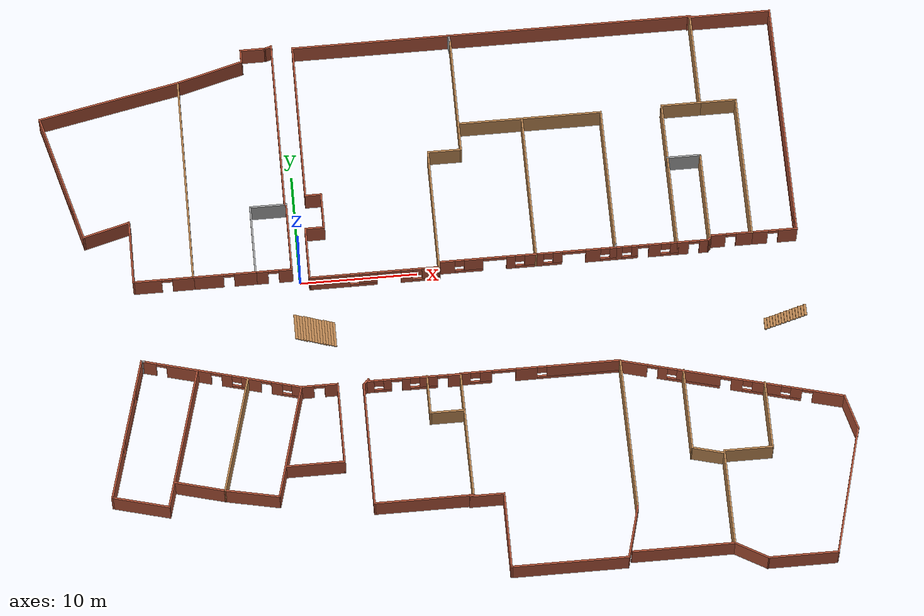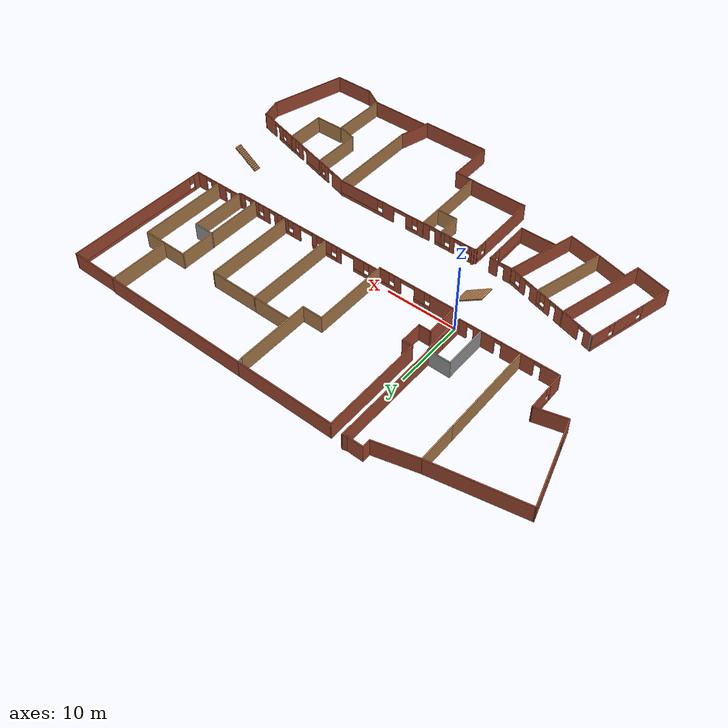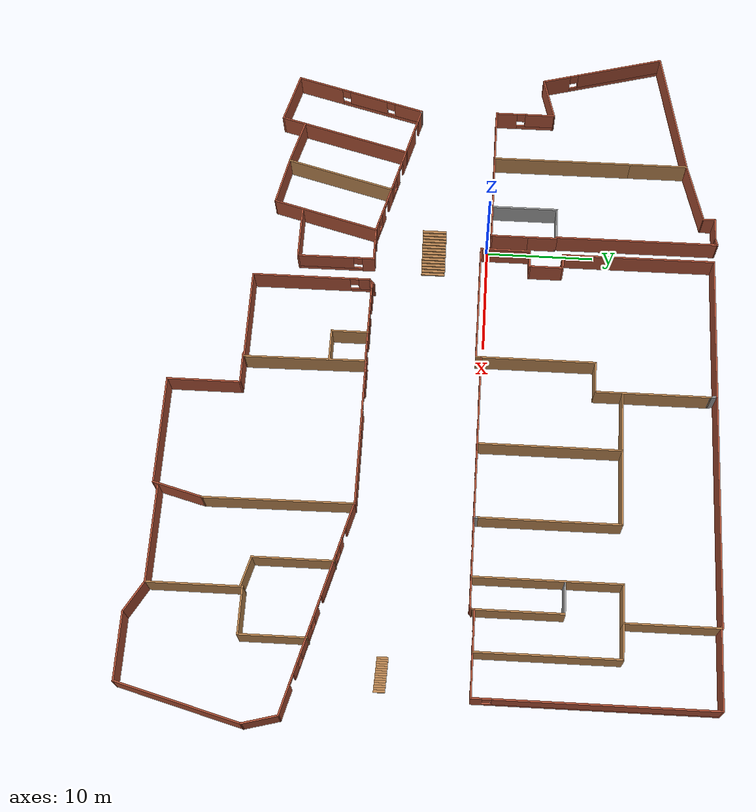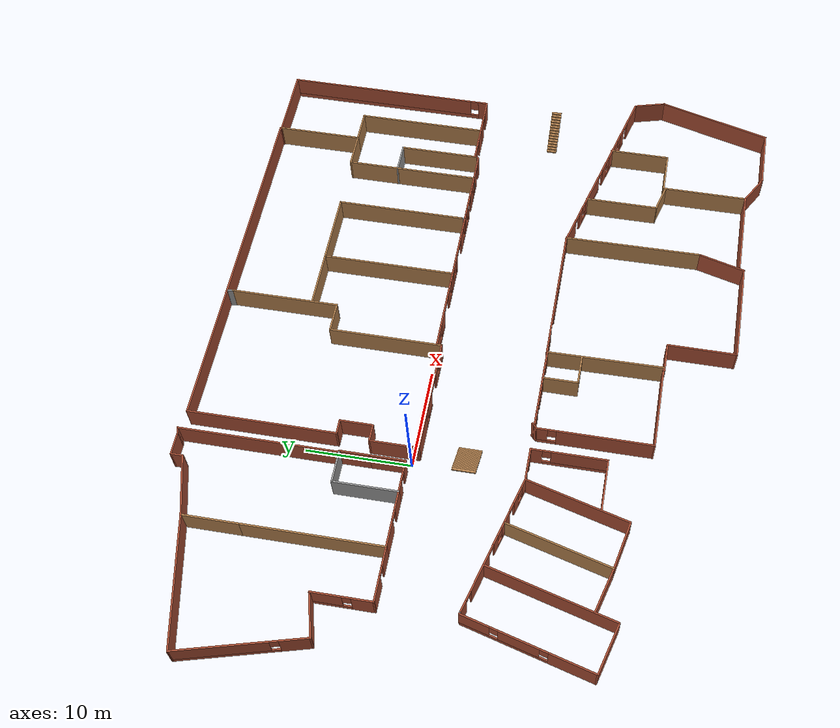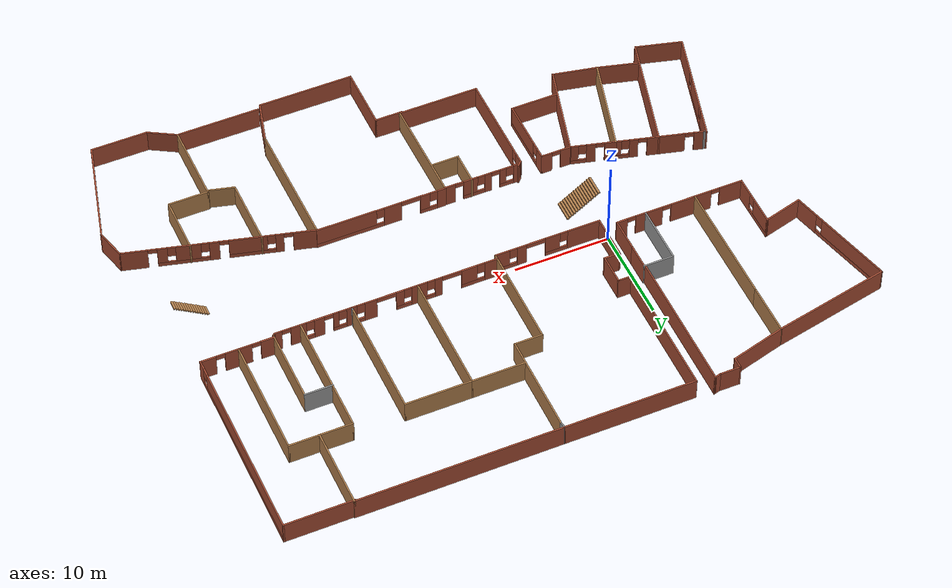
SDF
<?xml version='1.0'?>
<sdf version='1.6'>
  <model name='vital'>
    <pose frame=''>12.2387 -3.95497 0 0 -0 0</pose>
    <link name='Stairs_0'>
      <visual name='Stairs_0_Visual_0'>
        <pose frame=''>-9.74123 -1.05523 0.083333 0 -0 -1.5708</pose>
        <geometry>
          <box>
            <size>2.22056 0.233333 0.166667</size>
          </box>
        </geometry>
        <material>
          <script>
            <uri>file://media/materials/scripts/gazebo.material</uri>
            <name>Gazebo/Wood</name>
          </script>
          <ambient>1 1 1 1</ambient>
        </material>
      </visual>
      <collision name='Stairs_0_Collision_0'>
        <geometry>
          <box>
            <size>2.22056 0.233333 0.166667</size>
          </box>
        </geometry>
        <pose frame=''>-9.74123 -1.05523 0.083333 0 -0 -1.5708</pose>
      </collision>
      <visual name='Stairs_0_Visual_1'>
        <pose frame=''>-9.97456 -1.05523 0.25 0 -0 -1.5708</pose>
        <geometry>
          <box>
            <size>2.22056 0.233333 0.166667</size>
          </box>
        </geometry>
        <material>
          <script>
            <uri>file://media/materials/scripts/gazebo.material</uri>
            <name>Gazebo/Wood</name>
          </script>
          <ambient>1 1 1 1</ambient>
        </material>
      </visual>
      <collision name='Stairs_0_Collision_1'>
        <geometry>
          <box>
            <size>2.22056 0.233333 0.166667</size>
          </box>
        </geometry>
        <pose frame=''>-9.97456 -1.05523 0.25 0 -0 -1.5708</pose>
      </collision>
      <visual name='Stairs_0_Visual_2'>
        <pose frame=''>-10.2079 -1.05523 0.416667 0 -0 -1.5708</pose>
        <geometry>
          <box>
            <size>2.22056 0.233333 0.166667</size>
          </box>
        </geometry>
        <material>
          <script>
            <uri>file://media/materials/scripts/gazebo.material</uri>
            <name>Gazebo/Wood</name>
          </script>
          <ambient>1 1 1 1</ambient>
        </material>
      </visual>
      <collision name='Stairs_0_Collision_2'>
        <geometry>
          <box>
            <size>2.22056 0.233333 0.166667</size>
          </box>
        </geometry>
        <pose frame=''>-10.2079 -1.05523 0.416667 0 -0 -1.5708</pose>
      </collision>
      <visual name='Stairs_0_Visual_3'>
        <pose frame=''>-10.4412 -1.05523 0.583333 0 -0 -1.5708</pose>
        <geometry>
          <box>
            <size>2.22056 0.233333 0.166667</size>
          </box>
        </geometry>
        <material>
          <script>
            <uri>file://media/materials/scripts/gazebo.material</uri>
            <name>Gazebo/Wood</name>
          </script>
          <ambient>1 1 1 1</ambient>
        </material>
      </visual>
      <collision name='Stairs_0_Collision_3'>
        <geometry>
          <box>
            <size>2.22056 0.233333 0.166667</size>
          </box>
        </geometry>
        <pose frame=''>-10.4412 -1.05523 0.583333 0 -0 -1.5708</pose>
      </collision>
      <visual name='Stairs_0_Visual_4'>
        <pose frame=''>-10.6746 -1.05523 0.75 0 -0 -1.5708</pose>
        <geometry>
          <box>
            <size>2.22056 0.233333 0.166667</size>
          </box>
        </geometry>
        <material>
          <script>
            <uri>file://media/materials/scripts/gazebo.material</uri>
            <name>Gazebo/Wood</name>
          </script>
          <ambient>1 1 1 1</ambient>
        </material>
      </visual>
      <collision name='Stairs_0_Collision_4'>
        <geometry>
          <box>
            <size>2.22056 0.233333 0.166667</size>
          </box>
        </geometry>
        <pose frame=''>-10.6746 -1.05523 0.75 0 -0 -1.5708</pose>
      </collision>
      <visual name='Stairs_0_Visual_5'>
        <pose frame=''>-10.9079 -1.05523 0.916667 0 -0 -1.5708</pose>
        <geometry>
          <box>
            <size>2.22056 0.233333 0.166667</size>
          </box>
        </geometry>
        <material>
          <script>
            <uri>file://media/materials/scripts/gazebo.material</uri>
            <name>Gazebo/Wood</name>
          </script>
          <ambient>1 1 1 1</ambient>
        </material>
      </visual>
      <collision name='Stairs_0_Collision_5'>
        <geometry>
          <box>
            <size>2.22056 0.233333 0.166667</size>
          </box>
        </geometry>
        <pose frame=''>-10.9079 -1.05523 0.916667 0 -0 -1.5708</pose>
      </collision>
      <visual name='Stairs_0_Visual_6'>
        <pose frame=''>-11.1412 -1.05523 1.08333 0 -0 -1.5708</pose>
        <geometry>
          <box>
            <size>2.22056 0.233333 0.166667</size>
          </box>
        </geometry>
        <material>
          <script>
            <uri>file://media/materials/scripts/gazebo.material</uri>
            <name>Gazebo/Wood</name>
          </script>
          <ambient>1 1 1 1</ambient>
        </material>
      </visual>
      <collision name='Stairs_0_Collision_6'>
        <geometry>
          <box>
            <size>2.22056 0.233333 0.166667</size>
          </box>
        </geometry>
        <pose frame=''>-11.1412 -1.05523 1.08333 0 -0 -1.5708</pose>
      </collision>
      <visual name='Stairs_0_Visual_7'>
        <pose frame=''>-11.3746 -1.05523 1.25 0 -0 -1.5708</pose>
        <geometry>
          <box>
            <size>2.22056 0.233333 0.166667</size>
          </box>
        </geometry>
        <material>
          <script>
            <uri>file://media/materials/scripts/gazebo.material</uri>
            <name>Gazebo/Wood</name>
          </script>
          <ambient>1 1 1 1</ambient>
        </material>
      </visual>
      <collision name='Stairs_0_Collision_7'>
        <geometry>
          <box>
            <size>2.22056 0.233333 0.166667</size>
          </box>
        </geometry>
        <pose frame=''>-11.3746 -1.05523 1.25 0 -0 -1.5708</pose>
      </collision>
      <visual name='Stairs_0_Visual_8'>
        <pose frame=''>-11.6079 -1.05523 1.41667 0 -0 -1.5708</pose>
        <geometry>
          <box>
            <size>2.22056 0.233333 0.166667</size>
          </box>
        </geometry>
        <material>
          <script>
            <uri>file://media/materials/scripts/gazebo.material</uri>
            <name>Gazebo/Wood</name>
          </script>
          <ambient>1 1 1 1</ambient>
        </material>
      </visual>
      <collision name='Stairs_0_Collision_8'>
        <geometry>
          <box>
            <size>2.22056 0.233333 0.166667</size>
          </box>
        </geometry>
        <pose frame=''>-11.6079 -1.05523 1.41667 0 -0 -1.5708</pose>
      </collision>
      <visual name='Stairs_0_Visual_9'>
        <pose frame=''>-11.8412 -1.05523 1.58333 0 -0 -1.5708</pose>
        <geometry>
          <box>
            <size>2.22056 0.233333 0.166667</size>
          </box>
        </geometry>
        <material>
          <script>
            <uri>file://media/materials/scripts/gazebo.material</uri>
            <name>Gazebo/Wood</name>
          </script>
          <ambient>1 1 1 1</ambient>
        </material>
      </visual>
      <collision name='Stairs_0_Collision_9'>
        <geometry>
          <box>
            <size>2.22056 0.233333 0.166667</size>
          </box>
        </geometry>
        <pose frame=''>-11.8412 -1.05523 1.58333 0 -0 -1.5708</pose>
      </collision>
      <visual name='Stairs_0_Visual_10'>
        <pose frame=''>-12.0746 -1.05523 1.75 0 -0 -1.5708</pose>
        <geometry>
          <box>
            <size>2.22056 0.233333 0.166667</size>
          </box>
        </geometry>
        <material>
          <script>
            <uri>file://media/materials/scripts/gazebo.material</uri>
            <name>Gazebo/Wood</name>
          </script>
          <ambient>1 1 1 1</ambient>
        </material>
      </visual>
      <collision name='Stairs_0_Collision_10'>
        <geometry>
          <box>
            <size>2.22056 0.233333 0.166667</size>
          </box>
        </geometry>
        <pose frame=''>-12.0746 -1.05523 1.75 0 -0 -1.5708</pose>
      </collision>
      <visual name='Stairs_0_Visual_11'>
        <pose frame=''>-12.3079 -1.05523 1.91667 0 -0 -1.5708</pose>
        <geometry>
          <box>
            <size>2.22056 0.233333 0.166667</size>
          </box>
        </geometry>
        <material>
          <script>
            <uri>file://media/materials/scripts/gazebo.material</uri>
            <name>Gazebo/Wood</name>
          </script>
          <ambient>1 1 1 1</ambient>
        </material>
      </visual>
      <collision name='Stairs_0_Collision_11'>
        <geometry>
          <box>
            <size>2.22056 0.233333 0.166667</size>
          </box>
        </geometry>
        <pose frame=''>-12.3079 -1.05523 1.91667 0 -0 -1.5708</pose>
      </collision>
      <visual name='Stairs_0_Visual_12'>
        <pose frame=''>-12.5412 -1.05523 2.08333 0 -0 -1.5708</pose>
        <geometry>
          <box>
            <size>2.22056 0.233333 0.166667</size>
          </box>
        </geometry>
        <material>
          <script>
            <uri>file://media/materials/scripts/gazebo.material</uri>
            <name>Gazebo/Wood</name>
          </script>
          <ambient>1 1 1 1</ambient>
        </material>
      </visual>
      <collision name='Stairs_0_Collision_12'>
        <geometry>
          <box>
            <size>2.22056 0.233333 0.166667</size>
          </box>
        </geometry>
        <pose frame=''>-12.5412 -1.05523 2.08333 0 -0 -1.5708</pose>
      </collision>
      <visual name='Stairs_0_Visual_13'>
        <pose frame=''>-12.7746 -1.05523 2.25 0 -0 -1.5708</pose>
        <geometry>
          <box>
            <size>2.22056 0.233333 0.166667</size>
          </box>
        </geometry>
        <material>
          <script>
            <uri>file://media/materials/scripts/gazebo.material</uri>
            <name>Gazebo/Wood</name>
          </script>
          <ambient>1 1 1 1</ambient>
        </material>
      </visual>
      <collision name='Stairs_0_Collision_13'>
        <geometry>
          <box>
            <size>2.22056 0.233333 0.166667</size>
          </box>
        </geometry>
        <pose frame=''>-12.7746 -1.05523 2.25 0 -0 -1.5708</pose>
      </collision>
      <visual name='Stairs_0_Visual_14'>
        <pose frame=''>-13.0079 -1.05522 2.41667 0 -0 -1.5708</pose>
        <geometry>
          <box>
            <size>2.22056 0.233333 0.166667</size>
          </box>
        </geometry>
        <material>
          <script>
            <uri>file://media/materials/scripts/gazebo.material</uri>
            <name>Gazebo/Wood</name>
          </script>
          <ambient>1 1 1 1</ambient>
        </material>
      </visual>
      <collision name='Stairs_0_Collision_14'>
        <geometry>
          <box>
            <size>2.22056 0.233333 0.166667</size>
          </box>
        </geometry>
        <pose frame=''>-13.0079 -1.05522 2.41667 0 -0 -1.5708</pose>
      </collision>
    </link>
    <link name='Stairs_1'>
      <visual name='Stairs_1_Visual_0'>
        <pose frame=''>27.018 -3.37906 0.083333 0 -0 1.5708</pose>
        <geometry>
          <box>
            <size>1 0.233333 0.166667</size>
          </box>
        </geometry>
        <material>
          <script>
            <uri>file://media/materials/scripts/gazebo.material</uri>
            <name>Gazebo/Wood</name>
          </script>
          <ambient>1 1 1 1</ambient>
        </material>
      </visual>
      <collision name='Stairs_1_Collision_0'>
        <geometry>
          <box>
            <size>1 0.233333 0.166667</size>
          </box>
        </geometry>
        <pose frame=''>27.018 -3.37906 0.083333 0 -0 1.5708</pose>
      </collision>
      <visual name='Stairs_1_Visual_1'>
        <pose frame=''>27.2513 -3.37906 0.25 0 -0 1.5708</pose>
        <geometry>
          <box>
            <size>1 0.233333 0.166667</size>
          </box>
        </geometry>
        <material>
          <script>
            <uri>file://media/materials/scripts/gazebo.material</uri>
            <name>Gazebo/Wood</name>
          </script>
          <ambient>1 1 1 1</ambient>
        </material>
      </visual>
      <collision name='Stairs_1_Collision_1'>
        <geometry>
          <box>
            <size>1 0.233333 0.166667</size>
          </box>
        </geometry>
        <pose frame=''>27.2513 -3.37906 0.25 0 -0 1.5708</pose>
      </collision>
      <visual name='Stairs_1_Visual_2'>
        <pose frame=''>27.4847 -3.37906 0.416667 0 -0 1.5708</pose>
        <geometry>
          <box>
            <size>1 0.233333 0.166667</size>
          </box>
        </geometry>
        <material>
          <script>
            <uri>file://media/materials/scripts/gazebo.material</uri>
            <name>Gazebo/Wood</name>
          </script>
          <ambient>1 1 1 1</ambient>
        </material>
      </visual>
      <collision name='Stairs_1_Collision_2'>
        <geometry>
          <box>
            <size>1 0.233333 0.166667</size>
          </box>
        </geometry>
        <pose frame=''>27.4847 -3.37906 0.416667 0 -0 1.5708</pose>
      </collision>
      <visual name='Stairs_1_Visual_3'>
        <pose frame=''>27.718 -3.37906 0.583333 0 -0 1.5708</pose>
        <geometry>
          <box>
            <size>1 0.233333 0.166667</size>
          </box>
        </geometry>
        <material>
          <script>
            <uri>file://media/materials/scripts/gazebo.material</uri>
            <name>Gazebo/Wood</name>
          </script>
          <ambient>1 1 1 1</ambient>
        </material>
      </visual>
      <collision name='Stairs_1_Collision_3'>
        <geometry>
          <box>
            <size>1 0.233333 0.166667</size>
          </box>
        </geometry>
        <pose frame=''>27.718 -3.37906 0.583333 0 -0 1.5708</pose>
      </collision>
      <visual name='Stairs_1_Visual_4'>
        <pose frame=''>27.9513 -3.37906 0.75 0 -0 1.5708</pose>
        <geometry>
          <box>
            <size>1 0.233333 0.166667</size>
          </box>
        </geometry>
        <material>
          <script>
            <uri>file://media/materials/scripts/gazebo.material</uri>
            <name>Gazebo/Wood</name>
          </script>
          <ambient>1 1 1 1</ambient>
        </material>
      </visual>
      <collision name='Stairs_1_Collision_4'>
        <geometry>
          <box>
            <size>1 0.233333 0.166667</size>
          </box>
        </geometry>
        <pose frame=''>27.9513 -3.37906 0.75 0 -0 1.5708</pose>
      </collision>
      <visual name='Stairs_1_Visual_5'>
        <pose frame=''>28.1847 -3.37906 0.916667 0 -0 1.5708</pose>
        <geometry>
          <box>
            <size>1 0.233333 0.166667</size>
          </box>
        </geometry>
        <material>
          <script>
            <uri>file://media/materials/scripts/gazebo.material</uri>
            <name>Gazebo/Wood</name>
          </script>
          <ambient>1 1 1 1</ambient>
        </material>
      </visual>
      <collision name='Stairs_1_Collision_5'>
        <geometry>
          <box>
            <size>1 0.233333 0.166667</size>
          </box>
        </geometry>
        <pose frame=''>28.1847 -3.37906 0.916667 0 -0 1.5708</pose>
      </collision>
      <visual name='Stairs_1_Visual_6'>
        <pose frame=''>28.418 -3.37906 1.08333 0 -0 1.5708</pose>
        <geometry>
          <box>
            <size>1 0.233333 0.166667</size>
          </box>
        </geometry>
        <material>
          <script>
            <uri>file://media/materials/scripts/gazebo.material</uri>
            <name>Gazebo/Wood</name>
          </script>
          <ambient>1 1 1 1</ambient>
        </material>
      </visual>
      <collision name='Stairs_1_Collision_6'>
        <geometry>
          <box>
            <size>1 0.233333 0.166667</size>
          </box>
        </geometry>
        <pose frame=''>28.418 -3.37906 1.08333 0 -0 1.5708</pose>
      </collision>
      <visual name='Stairs_1_Visual_7'>
        <pose frame=''>28.6513 -3.37906 1.25 0 -0 1.5708</pose>
        <geometry>
          <box>
            <size>1 0.233333 0.166667</size>
          </box>
        </geometry>
        <material>
          <script>
            <uri>file://media/materials/scripts/gazebo.material</uri>
            <name>Gazebo/Wood</name>
          </script>
          <ambient>1 1 1 1</ambient>
        </material>
      </visual>
      <collision name='Stairs_1_Collision_7'>
        <geometry>
          <box>
            <size>1 0.233333 0.166667</size>
          </box>
        </geometry>
        <pose frame=''>28.6513 -3.37906 1.25 0 -0 1.5708</pose>
      </collision>
      <visual name='Stairs_1_Visual_8'>
        <pose frame=''>28.8847 -3.37906 1.41667 0 -0 1.5708</pose>
        <geometry>
          <box>
            <size>1 0.233333 0.166667</size>
          </box>
        </geometry>
        <material>
          <script>
            <uri>file://media/materials/scripts/gazebo.material</uri>
            <name>Gazebo/Wood</name>
          </script>
          <ambient>1 1 1 1</ambient>
        </material>
      </visual>
      <collision name='Stairs_1_Collision_8'>
        <geometry>
          <box>
            <size>1 0.233333 0.166667</size>
          </box>
        </geometry>
        <pose frame=''>28.8847 -3.37906 1.41667 0 -0 1.5708</pose>
      </collision>
      <visual name='Stairs_1_Visual_9'>
        <pose frame=''>29.118 -3.37906 1.58333 0 -0 1.5708</pose>
        <geometry>
          <box>
            <size>1 0.233333 0.166667</size>
          </box>
        </geometry>
        <material>
          <script>
            <uri>file://media/materials/scripts/gazebo.material</uri>
            <name>Gazebo/Wood</name>
          </script>
          <ambient>1 1 1 1</ambient>
        </material>
      </visual>
      <collision name='Stairs_1_Collision_9'>
        <geometry>
          <box>
            <size>1 0.233333 0.166667</size>
          </box>
        </geometry>
        <pose frame=''>29.118 -3.37906 1.58333 0 -0 1.5708</pose>
      </collision>
      <visual name='Stairs_1_Visual_10'>
        <pose frame=''>29.3513 -3.37906 1.75 0 -0 1.5708</pose>
        <geometry>
          <box>
            <size>1 0.233333 0.166667</size>
          </box>
        </geometry>
        <material>
          <script>
            <uri>file://media/materials/scripts/gazebo.material</uri>
            <name>Gazebo/Wood</name>
          </script>
          <ambient>1 1 1 1</ambient>
        </material>
      </visual>
      <collision name='Stairs_1_Collision_10'>
        <geometry>
          <box>
            <size>1 0.233333 0.166667</size>
          </box>
        </geometry>
        <pose frame=''>29.3513 -3.37906 1.75 0 -0 1.5708</pose>
      </collision>
      <visual name='Stairs_1_Visual_11'>
        <pose frame=''>29.5847 -3.37906 1.91667 0 -0 1.5708</pose>
        <geometry>
          <box>
            <size>1 0.233333 0.166667</size>
          </box>
        </geometry>
        <material>
          <script>
            <uri>file://media/materials/scripts/gazebo.material</uri>
            <name>Gazebo/Wood</name>
          </script>
          <ambient>1 1 1 1</ambient>
        </material>
      </visual>
      <collision name='Stairs_1_Collision_11'>
        <geometry>
          <box>
            <size>1 0.233333 0.166667</size>
          </box>
        </geometry>
        <pose frame=''>29.5847 -3.37906 1.91667 0 -0 1.5708</pose>
      </collision>
      <visual name='Stairs_1_Visual_12'>
        <pose frame=''>29.818 -3.37906 2.08333 0 -0 1.5708</pose>
        <geometry>
          <box>
            <size>1 0.233333 0.166667</size>
          </box>
        </geometry>
        <material>
          <script>
            <uri>file://media/materials/scripts/gazebo.material</uri>
            <name>Gazebo/Wood</name>
          </script>
          <ambient>1 1 1 1</ambient>
        </material>
      </visual>
      <collision name='Stairs_1_Collision_12'>
        <geometry>
          <box>
            <size>1 0.233333 0.166667</size>
          </box>
        </geometry>
        <pose frame=''>29.818 -3.37906 2.08333 0 -0 1.5708</pose>
      </collision>
      <visual name='Stairs_1_Visual_13'>
        <pose frame=''>30.0513 -3.37906 2.25 0 -0 1.5708</pose>
        <geometry>
          <box>
            <size>1 0.233333 0.166667</size>
          </box>
        </geometry>
        <material>
          <script>
            <uri>file://media/materials/scripts/gazebo.material</uri>
            <name>Gazebo/Wood</name>
          </script>
          <ambient>1 1 1 1</ambient>
        </material>
      </visual>
      <collision name='Stairs_1_Collision_13'>
        <geometry>
          <box>
            <size>1 0.233333 0.166667</size>
          </box>
        </geometry>
        <pose frame=''>30.0513 -3.37906 2.25 0 -0 1.5708</pose>
      </collision>
      <visual name='Stairs_1_Visual_14'>
        <pose frame=''>30.2847 -3.37905 2.41667 0 -0 1.5708</pose>
        <geometry>
          <box>
            <size>1 0.233333 0.166667</size>
          </box>
        </geometry>
        <material>
          <script>
            <uri>file://media/materials/scripts/gazebo.material</uri>
            <name>Gazebo/Wood</name>
          </script>
          <ambient>1 1 1 1</ambient>
        </material>
      </visual>
      <collision name='Stairs_1_Collision_14'>
        <geometry>
          <box>
            <size>1 0.233333 0.166667</size>
          </box>
        </geometry>
        <pose frame=''>30.2847 -3.37905 2.41667 0 -0 1.5708</pose>
      </collision>
    </link>
    <link name='Wall_100'>
      <collision name='Wall_100_Collision'>
        <geometry>
          <box>
            <size>5 0.15 2.5</size>
          </box>
        </geometry>
        <pose frame=''>0 0 1.25 0 -0 0</pose>
      </collision>
      <visual name='Wall_100_Visual'>
        <pose frame=''>0 0 1.25 0 -0 0</pose>
        <geometry>
          <box>
            <size>5 0.15 2.5</size>
          </box>
        </geometry>
        <material>
          <script>
            <uri>file://media/materials/scripts/gazebo.material</uri>
            <name>Gazebo/Bricks</name>
          </script>
          <ambient>1 1 1 1</ambient>
        </material>
      </visual>
      <pose frame=''>-27.234 -15.8492 0 0 -0 2.87979</pose>
    </link>
    <link name='Wall_101'>
      <pose frame=''>-27.9458 -9.13623 0 0 -0 1.309</pose>
      <visual name='Wall_101_Visual_0'>
        <pose frame=''>-4.12668 0 1.25 0 -0 0</pose>
        <geometry>
          <box>
            <size>4.49665 0.15 2.5</size>
          </box>
        </geometry>
        <material>
          <script>
            <uri>file://media/materials/scripts/gazebo.material</uri>
            <name>Gazebo/Bricks</name>
          </script>
          <ambient>1 1 1 1</ambient>
        </material>
      </visual>
      <collision name='Wall_101_Collision_0'>
        <geometry>
          <box>
            <size>4.49665 0.15 2.5</size>
          </box>
        </geometry>
        <pose frame=''>-4.12668 0 1.25 0 -0 0</pose>
      </collision>
      <visual name='Wall_101_Visual_1'>
        <pose frame=''>2.24832 0 0.25 0 -0 0</pose>
        <geometry>
          <box>
            <size>8.25336 0.15 0.5</size>
          </box>
        </geometry>
        <material>
          <script>
            <uri>file://media/materials/scripts/gazebo.material</uri>
            <name>Gazebo/Bricks</name>
          </script>
          <ambient>1 1 1 1</ambient>
        </material>
      </visual>
      <collision name='Wall_101_Collision_1'>
        <geometry>
          <box>
            <size>8.25336 0.15 0.5</size>
          </box>
        </geometry>
        <pose frame=''>2.24832 0 0.25 0 -0 0</pose>
      </collision>
      <visual name='Wall_101_Visual_2'>
        <pose frame=''>0.830511 0 1.5 0 -0 0</pose>
        <geometry>
          <box>
            <size>3.81773 0.15 2</size>
          </box>
        </geometry>
        <material>
          <script>
            <uri>file://media/materials/scripts/gazebo.material</uri>
            <name>Gazebo/Bricks</name>
          </script>
          <ambient>1 1 1 1</ambient>
        </material>
      </visual>
      <collision name='Wall_101_Collision_2'>
        <geometry>
          <box>
            <size>3.81773 0.15 2</size>
          </box>
        </geometry>
        <pose frame=''>0.830511 0 1.5 0 -0 0</pose>
      </collision>
      <visual name='Wall_101_Visual_3'>
        <pose frame=''>4.95719 0 1.5 0 -0 0</pose>
        <geometry>
          <box>
            <size>2.83562 0.15 2</size>
          </box>
        </geometry>
        <material>
          <script>
            <uri>file://media/materials/scripts/gazebo.material</uri>
            <name>Gazebo/Bricks</name>
          </script>
          <ambient>1 1 1 1</ambient>
        </material>
      </visual>
      <collision name='Wall_101_Collision_3'>
        <geometry>
          <box>
            <size>2.83562 0.15 2</size>
          </box>
        </geometry>
        <pose frame=''>4.95719 0 1.5 0 -0 0</pose>
      </collision>
      <visual name='Wall_101_Visual_4'>
        <pose frame=''>-1.47836 0 1.9 0 -0 0</pose>
        <geometry>
          <box>
            <size>0.8 0.15 1.2</size>
          </box>
        </geometry>
        <material>
          <script>
            <uri>file://media/materials/scripts/gazebo.material</uri>
            <name>Gazebo/Bricks</name>
          </script>
          <ambient>1 1 1 1</ambient>
        </material>
      </visual>
      <collision name='Wall_101_Collision_4'>
        <geometry>
          <box>
            <size>0.8 0.15 1.2</size>
          </box>
        </geometry>
        <pose frame=''>-1.47836 0 1.9 0 -0 0</pose>
      </collision>
      <visual name='Wall_101_Visual_5'>
        <pose frame=''>3.13938 0 1.9 0 -0 0</pose>
        <geometry>
          <box>
            <size>0.8 0.15 1.2</size>
          </box>
        </geometry>
        <material>
          <script>
            <uri>file://media/materials/scripts/gazebo.material</uri>
            <name>Gazebo/Bricks</name>
          </script>
          <ambient>1 1 1 1</ambient>
        </material>
      </visual>
      <collision name='Wall_101_Collision_5'>
        <geometry>
          <box>
            <size>0.8 0.15 1.2</size>
          </box>
        </geometry>
        <pose frame=''>3.13938 0 1.9 0 -0 0</pose>
      </collision>
    </link>
    <link name='Wall_102'>
      <collision name='Wall_102_Collision'>
        <geometry>
          <box>
            <size>0.4 0.15 2.5</size>
          </box>
        </geometry>
        <pose frame=''>0 0 1.25 0 -0 0</pose>
      </collision>
      <visual name='Wall_102_Visual'>
        <pose frame=''>0 0 1.25 0 -0 0</pose>
        <geometry>
          <box>
            <size>0.4 0.15 2.5</size>
          </box>
        </geometry>
        <material>
          <script>
            <uri>file://media/materials/scripts/gazebo.material</uri>
            <name>Gazebo/Grey</name>
          </script>
          <ambient>1 1 1 1</ambient>
        </material>
      </visual>
      <pose frame=''>-26.1945 -3.08325 0 0 0 -0.261799</pose>
    </link>
    <link name='Wall_104'>
      <pose frame=''>-19.5297 -4.8691 0 0 0 -0.261799</pose>
      <visual name='Wall_104_Visual_0'>
        <pose frame=''>-1.62247 0 1.25 0 -0 0</pose>
        <geometry>
          <box>
            <size>1.25506 0.15 2.5</size>
          </box>
        </geometry>
        <material>
          <script>
            <uri>file://media/materials/scripts/gazebo.material</uri>
            <name>Gazebo/Bricks</name>
          </script>
          <ambient>1 1 1 1</ambient>
        </material>
      </visual>
      <collision name='Wall_104_Collision_0'>
        <geometry>
          <box>
            <size>1.25506 0.15 2.5</size>
          </box>
        </geometry>
        <pose frame=''>-1.62247 0 1.25 0 -0 0</pose>
      </collision>
      <visual name='Wall_104_Visual_1'>
        <pose frame=''>0.350281 0 1.25 0 -0 0</pose>
        <geometry>
          <box>
            <size>0.890442 0.15 2.5</size>
          </box>
        </geometry>
        <material>
          <script>
            <uri>file://media/materials/scripts/gazebo.material</uri>
            <name>Gazebo/Bricks</name>
          </script>
          <ambient>1 1 1 1</ambient>
        </material>
      </visual>
      <collision name='Wall_104_Collision_1'>
        <geometry>
          <box>
            <size>0.890442 0.15 2.5</size>
          </box>
        </geometry>
        <pose frame=''>0.350281 0 1.25 0 -0 0</pose>
      </collision>
      <visual name='Wall_104_Visual_2'>
        <pose frame=''>1.52275 0 0.25 0 -0 0</pose>
        <geometry>
          <box>
            <size>1.4545 0.15 0.5</size>
          </box>
        </geometry>
        <material>
          <script>
            <uri>file://media/materials/scripts/gazebo.material</uri>
            <name>Gazebo/Bricks</name>
          </script>
          <ambient>1 1 1 1</ambient>
        </material>
      </visual>
      <collision name='Wall_104_Collision_2'>
        <geometry>
          <box>
            <size>1.4545 0.15 0.5</size>
          </box>
        </geometry>
        <pose frame=''>1.52275 0 0.25 0 -0 0</pose>
      </collision>
      <visual name='Wall_104_Visual_3'>
        <pose frame=''>1.92275 0 1.5 0 -0 0</pose>
        <geometry>
          <box>
            <size>0.654498 0.15 2</size>
          </box>
        </geometry>
        <material>
          <script>
            <uri>file://media/materials/scripts/gazebo.material</uri>
            <name>Gazebo/Bricks</name>
          </script>
          <ambient>1 1 1 1</ambient>
        </material>
      </visual>
      <collision name='Wall_104_Collision_3'>
        <geometry>
          <box>
            <size>0.654498 0.15 2</size>
          </box>
        </geometry>
        <pose frame=''>1.92275 0 1.5 0 -0 0</pose>
      </collision>
      <visual name='Wall_104_Visual_4'>
        <pose frame=''>1.1955 0 1.9 0 -0 0</pose>
        <geometry>
          <box>
            <size>0.8 0.15 1.2</size>
          </box>
        </geometry>
        <material>
          <script>
            <uri>file://media/materials/scripts/gazebo.material</uri>
            <name>Gazebo/Bricks</name>
          </script>
          <ambient>1 1 1 1</ambient>
        </material>
      </visual>
      <collision name='Wall_104_Collision_4'>
        <geometry>
          <box>
            <size>0.8 0.15 1.2</size>
          </box>
        </geometry>
        <pose frame=''>1.1955 0 1.9 0 -0 0</pose>
      </collision>
      <visual name='Wall_104_Visual_5'>
        <pose frame=''>-0.54494 0 2.25 0 -0 0</pose>
        <geometry>
          <box>
            <size>0.9 0.15 0.5</size>
          </box>
        </geometry>
        <material>
          <script>
            <uri>file://media/materials/scripts/gazebo.material</uri>
            <name>Gazebo/Bricks</name>
          </script>
          <ambient>1 1 1 1</ambient>
        </material>
      </visual>
      <collision name='Wall_104_Collision_5'>
        <geometry>
          <box>
            <size>0.9 0.15 0.5</size>
          </box>
        </geometry>
        <pose frame=''>-0.54494 0 2.25 0 -0 0</pose>
      </collision>
    </link>
    <link name='Wall_105'>
      <collision name='Wall_105_Collision'>
        <geometry>
          <box>
            <size>10.5 0.15 2.5</size>
          </box>
        </geometry>
        <pose frame=''>0 0 1.25 0 -0 0</pose>
      </collision>
      <visual name='Wall_105_Visual'>
        <pose frame=''>0 0 1.25 0 -0 0</pose>
        <geometry>
          <box>
            <size>10.5 0.15 2.5</size>
          </box>
        </geometry>
        <material>
          <script>
            <uri>file://media/materials/scripts/gazebo.material</uri>
            <name>Gazebo/Wood</name>
          </script>
          <ambient>1 1 1 1</ambient>
        </material>
      </visual>
      <pose frame=''>-18.7682 -10.4307 0 0 0 -1.8326</pose>
    </link>
    <link name='Wall_106'>
      <collision name='Wall_106_Collision'>
        <geometry>
          <box>
            <size>4.5 0.15 2.5</size>
          </box>
        </geometry>
        <pose frame=''>0 0 1.25 0 -0 0</pose>
      </collision>
      <visual name='Wall_106_Visual'>
        <pose frame=''>0 0 1.25 0 -0 0</pose>
        <geometry>
          <box>
            <size>4.5 0.15 2.5</size>
          </box>
        </geometry>
        <material>
          <script>
            <uri>file://media/materials/scripts/gazebo.material</uri>
            <name>Gazebo/Bricks</name>
          </script>
          <ambient>1 1 1 1</ambient>
        </material>
      </visual>
      <pose frame=''>-22.2084 -14.8664 0 0 -0 2.87979</pose>
    </link>
    <link name='Wall_108'>
      <pose frame=''>-15.2071 -6.02732 0 0 0 -0.261799</pose>
      <visual name='Wall_108_Visual_0'>
        <pose frame=''>-1.7708 0 1.25 0 -0 0</pose>
        <geometry>
          <box>
            <size>1.2084 0.15 2.5</size>
          </box>
        </geometry>
        <material>
          <script>
            <uri>file://media/materials/scripts/gazebo.material</uri>
            <name>Gazebo/Bricks</name>
          </script>
          <ambient>1 1 1 1</ambient>
        </material>
      </visual>
      <collision name='Wall_108_Collision_0'>
        <geometry>
          <box>
            <size>1.2084 0.15 2.5</size>
          </box>
        </geometry>
        <pose frame=''>-1.7708 0 1.25 0 -0 0</pose>
      </collision>
      <visual name='Wall_108_Visual_1'>
        <pose frame=''>0.199682 0 1.25 0 -0 0</pose>
        <geometry>
          <box>
            <size>0.932562 0.15 2.5</size>
          </box>
        </geometry>
        <material>
          <script>
            <uri>file://media/materials/scripts/gazebo.material</uri>
            <name>Gazebo/Bricks</name>
          </script>
          <ambient>1 1 1 1</ambient>
        </material>
      </visual>
      <collision name='Wall_108_Collision_1'>
        <geometry>
          <box>
            <size>0.932562 0.15 2.5</size>
          </box>
        </geometry>
        <pose frame=''>0.199682 0 1.25 0 -0 0</pose>
      </collision>
      <visual name='Wall_108_Visual_2'>
        <pose frame=''>1.52048 0 0.25 0 -0 0</pose>
        <geometry>
          <box>
            <size>1.70904 0.15 0.5</size>
          </box>
        </geometry>
        <material>
          <script>
            <uri>file://media/materials/scripts/gazebo.material</uri>
            <name>Gazebo/Bricks</name>
          </script>
          <ambient>1 1 1 1</ambient>
        </material>
      </visual>
      <collision name='Wall_108_Collision_2'>
        <geometry>
          <box>
            <size>1.70904 0.15 0.5</size>
          </box>
        </geometry>
        <pose frame=''>1.52048 0 0.25 0 -0 0</pose>
      </collision>
      <visual name='Wall_108_Visual_3'>
        <pose frame=''>1.92048 0 1.5 0 -0 0</pose>
        <geometry>
          <box>
            <size>0.909036 0.15 2</size>
          </box>
        </geometry>
        <material>
          <script>
            <uri>file://media/materials/scripts/gazebo.material</uri>
            <name>Gazebo/Bricks</name>
          </script>
          <ambient>1 1 1 1</ambient>
        </material>
      </visual>
      <collision name='Wall_108_Collision_3'>
        <geometry>
          <box>
            <size>0.909036 0.15 2</size>
          </box>
        </geometry>
        <pose frame=''>1.92048 0 1.5 0 -0 0</pose>
      </collision>
      <visual name='Wall_108_Visual_4'>
        <pose frame=''>1.06596 0 1.9 0 -0 0</pose>
        <geometry>
          <box>
            <size>0.8 0.15 1.2</size>
          </box>
        </geometry>
        <material>
          <script>
            <uri>file://media/materials/scripts/gazebo.material</uri>
            <name>Gazebo/Bricks</name>
          </script>
          <ambient>1 1 1 1</ambient>
        </material>
      </visual>
      <collision name='Wall_108_Collision_4'>
        <geometry>
          <box>
            <size>0.8 0.15 1.2</size>
          </box>
        </geometry>
        <pose frame=''>1.06596 0 1.9 0 -0 0</pose>
      </collision>
      <visual name='Wall_108_Visual_5'>
        <pose frame=''>-0.716599 0 2.25 0 -0 0</pose>
        <geometry>
          <box>
            <size>0.9 0.15 0.5</size>
          </box>
        </geometry>
        <material>
          <script>
            <uri>file://media/materials/scripts/gazebo.material</uri>
            <name>Gazebo/Bricks</name>
          </script>
          <ambient>1 1 1 1</ambient>
        </material>
      </visual>
      <collision name='Wall_108_Collision_5'>
        <geometry>
          <box>
            <size>0.9 0.15 0.5</size>
          </box>
        </geometry>
        <pose frame=''>-0.716599 0 2.25 0 -0 0</pose>
      </collision>
    </link>
    <link name='Wall_109'>
      <collision name='Wall_109_Collision'>
        <geometry>
          <box>
            <size>10.25 0.15 2.5</size>
          </box>
        </geometry>
        <pose frame=''>0 0 1.25 0 -0 0</pose>
      </collision>
      <visual name='Wall_109_Visual'>
        <pose frame=''>0 0 1.25 0 -0 0</pose>
        <geometry>
          <box>
            <size>10.25 0.15 2.5</size>
          </box>
        </geometry>
        <material>
          <script>
            <uri>file://media/materials/scripts/gazebo.material</uri>
            <name>Gazebo/Bricks</name>
          </script>
          <ambient>1 1 1 1</ambient>
        </material>
      </visual>
      <pose frame=''>-14.2925 -11.5005 0 0 0 -1.8326</pose>
    </link>
    <link name='Wall_110'>
      <collision name='Wall_110_Collision'>
        <geometry>
          <box>
            <size>4.75679 0.15 2.5</size>
          </box>
        </geometry>
        <pose frame=''>0 0 1.25 0 -0 0</pose>
      </collision>
      <visual name='Wall_110_Visual'>
        <pose frame=''>0 0 1.25 0 -0 0</pose>
        <geometry>
          <box>
            <size>4.75679 0.15 2.5</size>
          </box>
        </geometry>
        <material>
          <script>
            <uri>file://media/materials/scripts/gazebo.material</uri>
            <name>Gazebo/Bricks</name>
          </script>
          <ambient>1 1 1 1</ambient>
        </material>
      </visual>
      <pose frame=''>-17.8536 -15.9039 0 0 -0 2.93409</pose>
    </link>
    <link name='Wall_112'>
      <pose frame=''>-11.4355 -6.6226 0 0 -0 0</pose>
      <visual name='Wall_112_Visual_0'>
        <pose frame=''>-1.04973 0 1.25 0 -0 0</pose>
        <geometry>
          <box>
            <size>1.15054 0.15 2.5</size>
          </box>
        </geometry>
        <material>
          <script>
            <uri>file://media/materials/scripts/gazebo.material</uri>
            <name>Gazebo/Bricks</name>
          </script>
          <ambient>1 1 1 1</ambient>
        </material>
      </visual>
      <collision name='Wall_112_Collision_0'>
        <geometry>
          <box>
            <size>1.15054 0.15 2.5</size>
          </box>
        </geometry>
        <pose frame=''>-1.04973 0 1.25 0 -0 0</pose>
      </collision>
      <visual name='Wall_112_Visual_1'>
        <pose frame=''>1.02527 0 1.25 0 -0 0</pose>
        <geometry>
          <box>
            <size>1.19946 0.15 2.5</size>
          </box>
        </geometry>
        <material>
          <script>
            <uri>file://media/materials/scripts/gazebo.material</uri>
            <name>Gazebo/Bricks</name>
          </script>
          <ambient>1 1 1 1</ambient>
        </material>
      </visual>
      <collision name='Wall_112_Collision_1'>
        <geometry>
          <box>
            <size>1.19946 0.15 2.5</size>
          </box>
        </geometry>
        <pose frame=''>1.02527 0 1.25 0 -0 0</pose>
      </collision>
      <visual name='Wall_112_Visual_2'>
        <pose frame=''>-0.024462 0 2.25 0 -0 0</pose>
        <geometry>
          <box>
            <size>0.9 0.15 0.5</size>
          </box>
        </geometry>
        <material>
          <script>
            <uri>file://media/materials/scripts/gazebo.material</uri>
            <name>Gazebo/Bricks</name>
          </script>
          <ambient>1 1 1 1</ambient>
        </material>
      </visual>
      <collision name='Wall_112_Collision_2'>
        <geometry>
          <box>
            <size>0.9 0.15 0.5</size>
          </box>
        </geometry>
        <pose frame=''>-0.024462 0 2.25 0 -0 0</pose>
      </collision>
    </link>
    <link name='Wall_113'>
      <pose frame=''>-9.88551 -10.1726 0 0 0 -1.5708</pose>
      <visual name='Wall_113_Visual_0'>
        <pose frame=''>-3.04191 0 1.25 0 -0 0</pose>
        <geometry>
          <box>
            <size>1.16617 0.15 2.5</size>
          </box>
        </geometry>
        <material>
          <script>
            <uri>file://media/materials/scripts/gazebo.material</uri>
            <name>Gazebo/Bricks</name>
          </script>
          <ambient>1 1 1 1</ambient>
        </material>
      </visual>
      <collision name='Wall_113_Collision_0'>
        <geometry>
          <box>
            <size>1.16617 0.15 2.5</size>
          </box>
        </geometry>
        <pose frame=''>-3.04191 0 1.25 0 -0 0</pose>
      </collision>
      <visual name='Wall_113_Visual_1'>
        <pose frame=''>0.583086 0 0.25 0 -0 0</pose>
        <geometry>
          <box>
            <size>6.08383 0.15 0.5</size>
          </box>
        </geometry>
        <material>
          <script>
            <uri>file://media/materials/scripts/gazebo.material</uri>
            <name>Gazebo/Bricks</name>
          </script>
          <ambient>1 1 1 1</ambient>
        </material>
      </visual>
      <collision name='Wall_113_Collision_1'>
        <geometry>
          <box>
            <size>6.08383 0.15 0.5</size>
          </box>
        </geometry>
        <pose frame=''>0.583086 0 0.25 0 -0 0</pose>
      </collision>
      <visual name='Wall_113_Visual_2'>
        <pose frame=''>0.983086 0 1.5 0 -0 0</pose>
        <geometry>
          <box>
            <size>5.28383 0.15 2</size>
          </box>
        </geometry>
        <material>
          <script>
            <uri>file://media/materials/scripts/gazebo.material</uri>
            <name>Gazebo/Bricks</name>
          </script>
          <ambient>1 1 1 1</ambient>
        </material>
      </visual>
      <collision name='Wall_113_Collision_2'>
        <geometry>
          <box>
            <size>5.28383 0.15 2</size>
          </box>
        </geometry>
        <pose frame=''>0.983086 0 1.5 0 -0 0</pose>
      </collision>
      <visual name='Wall_113_Visual_3'>
        <pose frame=''>-2.05883 0 1.9 0 -0 0</pose>
        <geometry>
          <box>
            <size>0.8 0.15 1.2</size>
          </box>
        </geometry>
        <material>
          <script>
            <uri>file://media/materials/scripts/gazebo.material</uri>
            <name>Gazebo/Bricks</name>
          </script>
          <ambient>1 1 1 1</ambient>
        </material>
      </visual>
      <collision name='Wall_113_Collision_3'>
        <geometry>
          <box>
            <size>0.8 0.15 1.2</size>
          </box>
        </geometry>
        <pose frame=''>-2.05883 0 1.9 0 -0 0</pose>
      </collision>
    </link>
    <link name='Wall_114'>
      <collision name='Wall_114_Collision'>
        <geometry>
          <box>
            <size>5 0.15 2.5</size>
          </box>
        </geometry>
        <pose frame=''>0 0 1.25 0 -0 0</pose>
      </collision>
      <visual name='Wall_114_Visual'>
        <pose frame=''>0 0 1.25 0 -0 0</pose>
        <geometry>
          <box>
            <size>5 0.15 2.5</size>
          </box>
        </geometry>
        <material>
          <script>
            <uri>file://media/materials/scripts/gazebo.material</uri>
            <name>Gazebo/Bricks</name>
          </script>
          <ambient>1 1 1 1</ambient>
        </material>
      </visual>
      <pose frame=''>-12.3105 -13.7226 0 0 -0 3.14159</pose>
    </link>
    <link name='Wall_116'>
      <pose frame=''>-3.44702 -6.63306 0 0 0 -0.006694</pose>
      <visual name='Wall_116_Visual_0'>
        <pose frame=''>-3.71942 0 1.25 0 -0 0</pose>
        <geometry>
          <box>
            <size>0.704332 0.15 2.5</size>
          </box>
        </geometry>
        <material>
          <script>
            <uri>file://media/materials/scripts/gazebo.material</uri>
            <name>Gazebo/Bricks</name>
          </script>
          <ambient>1 1 1 1</ambient>
        </material>
      </visual>
      <collision name='Wall_116_Collision_0'>
        <geometry>
          <box>
            <size>0.704332 0.15 2.5</size>
          </box>
        </geometry>
        <pose frame=''>-3.71942 0 1.25 0 -0 0</pose>
      </collision>
      <visual name='Wall_116_Visual_1'>
        <pose frame=''>-0.624879 0 1.25 0 -0 0</pose>
        <geometry>
          <box>
            <size>0.697096 0.15 2.5</size>
          </box>
        </geometry>
        <material>
          <script>
            <uri>file://media/materials/scripts/gazebo.material</uri>
            <name>Gazebo/Bricks</name>
          </script>
          <ambient>1 1 1 1</ambient>
        </material>
      </visual>
      <collision name='Wall_116_Collision_1'>
        <geometry>
          <box>
            <size>0.697096 0.15 2.5</size>
          </box>
        </geometry>
        <pose frame=''>-0.624879 0 1.25 0 -0 0</pose>
      </collision>
      <visual name='Wall_116_Visual_2'>
        <pose frame=''>3.5022 0 1.25 0 -0 0</pose>
        <geometry>
          <box>
            <size>1.13877 0.15 2.5</size>
          </box>
        </geometry>
        <material>
          <script>
            <uri>file://media/materials/scripts/gazebo.material</uri>
            <name>Gazebo/Bricks</name>
          </script>
          <ambient>1 1 1 1</ambient>
        </material>
      </visual>
      <collision name='Wall_116_Collision_2'>
        <geometry>
          <box>
            <size>1.13877 0.15 2.5</size>
          </box>
        </geometry>
        <pose frame=''>3.5022 0 1.25 0 -0 0</pose>
      </collision>
      <visual name='Wall_116_Visual_3'>
        <pose frame=''>-2.62034 0 0.25 0 -0 0</pose>
        <geometry>
          <box>
            <size>1.49383 0.15 0.5</size>
          </box>
        </geometry>
        <material>
          <script>
            <uri>file://media/materials/scripts/gazebo.material</uri>
            <name>Gazebo/Bricks</name>
          </script>
          <ambient>1 1 1 1</ambient>
        </material>
      </visual>
      <collision name='Wall_116_Collision_3'>
        <geometry>
          <box>
            <size>1.49383 0.15 0.5</size>
          </box>
        </geometry>
        <pose frame=''>-2.62034 0 0.25 0 -0 0</pose>
      </collision>
      <visual name='Wall_116_Visual_4'>
        <pose frame=''>0.878245 0 0.25 0 -0 0</pose>
        <geometry>
          <box>
            <size>2.30915 0.15 0.5</size>
          </box>
        </geometry>
        <material>
          <script>
            <uri>file://media/materials/scripts/gazebo.material</uri>
            <name>Gazebo/Bricks</name>
          </script>
          <ambient>1 1 1 1</ambient>
        </material>
      </visual>
      <collision name='Wall_116_Collision_4'>
        <geometry>
          <box>
            <size>2.30915 0.15 0.5</size>
          </box>
        </geometry>
        <pose frame=''>0.878245 0 0.25 0 -0 0</pose>
      </collision>
      <visual name='Wall_116_Visual_5'>
        <pose frame=''>-2.22034 0 1.5 0 -0 0</pose>
        <geometry>
          <box>
            <size>0.693829 0.15 2</size>
          </box>
        </geometry>
        <material>
          <script>
            <uri>file://media/materials/scripts/gazebo.material</uri>
            <name>Gazebo/Bricks</name>
          </script>
          <ambient>1 1 1 1</ambient>
        </material>
      </visual>
      <collision name='Wall_116_Collision_5'>
        <geometry>
          <box>
            <size>0.693829 0.15 2</size>
          </box>
        </geometry>
        <pose frame=''>-2.22034 0 1.5 0 -0 0</pose>
      </collision>
      <visual name='Wall_116_Visual_6'>
        <pose frame=''>-2.22034 0 1.5 0 -0 0</pose>
        <geometry>
          <box>
            <size>0.693829 0.15 2</size>
          </box>
        </geometry>
        <material>
          <script>
            <uri>file://media/materials/scripts/gazebo.material</uri>
            <name>Gazebo/Bricks</name>
          </script>
          <ambient>1 1 1 1</ambient>
        </material>
      </visual>
      <collision name='Wall_116_Collision_6'>
        <geometry>
          <box>
            <size>0.693829 0.15 2</size>
          </box>
        </geometry>
        <pose frame=''>-2.22034 0 1.5 0 -0 0</pose>
      </collision>
      <visual name='Wall_116_Visual_7'>
        <pose frame=''>1.27825 0 1.5 0 -0 0</pose>
        <geometry>
          <box>
            <size>1.50915 0.15 2</size>
          </box>
        </geometry>
        <material>
          <script>
            <uri>file://media/materials/scripts/gazebo.material</uri>
            <name>Gazebo/Bricks</name>
          </script>
          <ambient>1 1 1 1</ambient>
        </material>
      </visual>
      <collision name='Wall_116_Collision_7'>
        <geometry>
          <box>
            <size>1.50915 0.15 2</size>
          </box>
        </geometry>
        <pose frame=''>1.27825 0 1.5 0 -0 0</pose>
      </collision>
      <visual name='Wall_116_Visual_8'>
        <pose frame=''>-2.96726 0 1.9 0 -0 0</pose>
        <geometry>
          <box>
            <size>0.8 0.15 1.2</size>
          </box>
        </geometry>
        <material>
          <script>
            <uri>file://media/materials/scripts/gazebo.material</uri>
            <name>Gazebo/Bricks</name>
          </script>
          <ambient>1 1 1 1</ambient>
        </material>
      </visual>
      <collision name='Wall_116_Collision_8'>
        <geometry>
          <box>
            <size>0.8 0.15 1.2</size>
          </box>
        </geometry>
        <pose frame=''>-2.96726 0 1.9 0 -0 0</pose>
      </collision>
      <visual name='Wall_116_Visual_9'>
        <pose frame=''>0.12367 0 1.9 0 -0 0</pose>
        <geometry>
          <box>
            <size>0.8 0.15 1.2</size>
          </box>
        </geometry>
        <material>
          <script>
            <uri>file://media/materials/scripts/gazebo.material</uri>
            <name>Gazebo/Bricks</name>
          </script>
          <ambient>1 1 1 1</ambient>
        </material>
      </visual>
      <collision name='Wall_116_Collision_9'>
        <geometry>
          <box>
            <size>0.8 0.15 1.2</size>
          </box>
        </geometry>
        <pose frame=''>0.12367 0 1.9 0 -0 0</pose>
      </collision>
      <visual name='Wall_116_Visual_10'>
        <pose frame=''>-1.42343 0 2.25 0 -0 0</pose>
        <geometry>
          <box>
            <size>0.9 0.15 0.5</size>
          </box>
        </geometry>
        <material>
          <script>
            <uri>file://media/materials/scripts/gazebo.material</uri>
            <name>Gazebo/Bricks</name>
          </script>
          <ambient>1 1 1 1</ambient>
        </material>
      </visual>
      <collision name='Wall_116_Collision_10'>
        <geometry>
          <box>
            <size>0.9 0.15 0.5</size>
          </box>
        </geometry>
        <pose frame=''>-1.42343 0 2.25 0 -0 0</pose>
      </collision>
      <visual name='Wall_116_Visual_11'>
        <pose frame=''>-1.42343 0 2.25 0 -0 0</pose>
        <geometry>
          <box>
            <size>0.9 0.15 0.5</size>
          </box>
        </geometry>
        <material>
          <script>
            <uri>file://media/materials/scripts/gazebo.material</uri>
            <name>Gazebo/Bricks</name>
          </script>
          <ambient>1 1 1 1</ambient>
        </material>
      </visual>
      <collision name='Wall_116_Collision_11'>
        <geometry>
          <box>
            <size>0.9 0.15 0.5</size>
          </box>
        </geometry>
        <pose frame=''>-1.42343 0 2.25 0 -0 0</pose>
      </collision>
      <visual name='Wall_116_Visual_12'>
        <pose frame=''>2.48282 0 2.25 0 -0 0</pose>
        <geometry>
          <box>
            <size>0.9 0.15 0.5</size>
          </box>
        </geometry>
        <material>
          <script>
            <uri>file://media/materials/scripts/gazebo.material</uri>
            <name>Gazebo/Bricks</name>
          </script>
          <ambient>1 1 1 1</ambient>
        </material>
      </visual>
      <collision name='Wall_116_Collision_12'>
        <geometry>
          <box>
            <size>0.9 0.15 0.5</size>
          </box>
        </geometry>
        <pose frame=''>2.48282 0 2.25 0 -0 0</pose>
      </collision>
    </link>
    <link name='Wall_117'>
      <collision name='Wall_117_Collision'>
        <geometry>
          <box>
            <size>11.197 0.15 2.5</size>
          </box>
        </geometry>
        <pose frame=''>0 0 1.25 0 -0 0</pose>
      </collision>
      <visual name='Wall_117_Visual'>
        <pose frame=''>0 0 1.25 0 -0 0</pose>
        <geometry>
          <box>
            <size>11.197 0.15 2.5</size>
          </box>
        </geometry>
        <material>
          <script>
            <uri>file://media/materials/scripts/gazebo.material</uri>
            <name>Gazebo/Wood</name>
          </script>
          <ambient>1 1 1 1</ambient>
        </material>
      </visual>
      <pose frame=''>0.602983 -12.1831 0 0 0 -1.56111</pose>
    </link>
    <link name='Wall_118'>
      <collision name='Wall_118_Collision'>
        <geometry>
          <box>
            <size>8.5 0.15 2.5</size>
          </box>
        </geometry>
        <pose frame=''>0 0 1.25 0 -0 0</pose>
      </collision>
      <visual name='Wall_118_Visual'>
        <pose frame=''>0 0 1.25 0 -0 0</pose>
        <geometry>
          <box>
            <size>8.5 0.15 2.5</size>
          </box>
        </geometry>
        <material>
          <script>
            <uri>file://media/materials/scripts/gazebo.material</uri>
            <name>Gazebo/Bricks</name>
          </script>
          <ambient>1 1 1 1</ambient>
        </material>
      </visual>
      <pose frame=''>-3.51851 -17.7063 0 0 -0 3.14159</pose>
    </link>
    <link name='Wall_119'>
      <pose frame=''>-7.69351 -12.2813 0 0 -0 1.5708</pose>
      <visual name='Wall_119_Visual_0'>
        <pose frame=''>-0.947604 0 1.25 0 -0 0</pose>
        <geometry>
          <box>
            <size>9.10479 0.15 2.5</size>
          </box>
        </geometry>
        <material>
          <script>
            <uri>file://media/materials/scripts/gazebo.material</uri>
            <name>Gazebo/Bricks</name>
          </script>
          <ambient>1 1 1 1</ambient>
        </material>
      </visual>
      <collision name='Wall_119_Collision_0'>
        <geometry>
          <box>
            <size>9.10479 0.15 2.5</size>
          </box>
        </geometry>
        <pose frame=''>-0.947604 0 1.25 0 -0 0</pose>
      </collision>
      <visual name='Wall_119_Visual_1'>
        <pose frame=''>4.5524 0 0.25 0 -0 0</pose>
        <geometry>
          <box>
            <size>1.89521 0.15 0.5</size>
          </box>
        </geometry>
        <material>
          <script>
            <uri>file://media/materials/scripts/gazebo.material</uri>
            <name>Gazebo/Bricks</name>
          </script>
          <ambient>1 1 1 1</ambient>
        </material>
      </visual>
      <collision name='Wall_119_Collision_1'>
        <geometry>
          <box>
            <size>1.89521 0.15 0.5</size>
          </box>
        </geometry>
        <pose frame=''>4.5524 0 0.25 0 -0 0</pose>
      </collision>
      <visual name='Wall_119_Visual_2'>
        <pose frame=''>4.9524 0 1.5 0 -0 0</pose>
        <geometry>
          <box>
            <size>1.09521 0.15 2</size>
          </box>
        </geometry>
        <material>
          <script>
            <uri>file://media/materials/scripts/gazebo.material</uri>
            <name>Gazebo/Bricks</name>
          </script>
          <ambient>1 1 1 1</ambient>
        </material>
      </visual>
      <collision name='Wall_119_Collision_2'>
        <geometry>
          <box>
            <size>1.09521 0.15 2</size>
          </box>
        </geometry>
        <pose frame=''>4.9524 0 1.5 0 -0 0</pose>
      </collision>
      <visual name='Wall_119_Visual_3'>
        <pose frame=''>4.00479 0 1.9 0 -0 0</pose>
        <geometry>
          <box>
            <size>0.8 0.15 1.2</size>
          </box>
        </geometry>
        <material>
          <script>
            <uri>file://media/materials/scripts/gazebo.material</uri>
            <name>Gazebo/Bricks</name>
          </script>
          <ambient>1 1 1 1</ambient>
        </material>
      </visual>
      <collision name='Wall_119_Collision_3'>
        <geometry>
          <box>
            <size>0.8 0.15 1.2</size>
          </box>
        </geometry>
        <pose frame=''>4.00479 0 1.9 0 -0 0</pose>
      </collision>
    </link>
    <link name='Wall_120'>
      <collision name='Wall_120_Collision'>
        <geometry>
          <box>
            <size>0.75 0.15 2.5</size>
          </box>
        </geometry>
        <pose frame=''>0 0 1.25 0 -0 0</pose>
      </collision>
      <visual name='Wall_120_Visual'>
        <pose frame=''>0 0 1.25 0 -0 0</pose>
        <geometry>
          <box>
            <size>0.75 0.15 2.5</size>
          </box>
        </geometry>
        <material>
          <script>
            <uri>file://media/materials/scripts/gazebo.material</uri>
            <name>Gazebo/Bricks</name>
          </script>
          <ambient>1 1 1 1</ambient>
        </material>
      </visual>
      <pose frame=''>-7.48138 -6.64417 0 0 -0 0.785398</pose>
    </link>
    <link name='Wall_122'>
      <collision name='Wall_122_Collision'>
        <geometry>
          <box>
            <size>3.5 0.15 2.5</size>
          </box>
        </geometry>
        <pose frame=''>0 0 1.25 0 -0 0</pose>
      </collision>
      <visual name='Wall_122_Visual'>
        <pose frame=''>0 0 1.25 0 -0 0</pose>
        <geometry>
          <box>
            <size>3.5 0.15 2.5</size>
          </box>
        </geometry>
        <material>
          <script>
            <uri>file://media/materials/scripts/gazebo.material</uri>
            <name>Gazebo/Wood</name>
          </script>
          <ambient>1 1 1 1</ambient>
        </material>
      </visual>
      <pose frame=''>-2.29682 -8.28131 0 0 0 -1.5708</pose>
    </link>
    <link name='Wall_123'>
      <collision name='Wall_123_Collision'>
        <geometry>
          <box>
            <size>3 0.15 2.5</size>
          </box>
        </geometry>
        <pose frame=''>0 0 1.25 0 -0 0</pose>
      </collision>
      <visual name='Wall_123_Visual'>
        <pose frame=''>0 0 1.25 0 -0 0</pose>
        <geometry>
          <box>
            <size>3 0.15 2.5</size>
          </box>
        </geometry>
        <material>
          <script>
            <uri>file://media/materials/scripts/gazebo.material</uri>
            <name>Gazebo/Wood</name>
          </script>
          <ambient>1 1 1 1</ambient>
        </material>
      </visual>
      <pose frame=''>-0.871823 -9.95631 0 0 -0 0</pose>
    </link>
    <link name='Wall_125'>
      <pose frame=''>7.34948 -6.60631 0 0 -0 0</pose>
      <visual name='Wall_125_Visual_0'>
        <pose frame=''>-6.41052 0 1.25 0 -0 0</pose>
        <geometry>
          <box>
            <size>0.928962 0.15 2.5</size>
          </box>
        </geometry>
        <material>
          <script>
            <uri>file://media/materials/scripts/gazebo.material</uri>
            <name>Gazebo/Bricks</name>
          </script>
          <ambient>1 1 1 1</ambient>
        </material>
      </visual>
      <collision name='Wall_125_Collision_0'>
        <geometry>
          <box>
            <size>0.928962 0.15 2.5</size>
          </box>
        </geometry>
        <pose frame=''>-6.41052 0 1.25 0 -0 0</pose>
      </collision>
      <visual name='Wall_125_Visual_1'>
        <pose frame=''>-1.17751 0 1.25 0 -0 0</pose>
        <geometry>
          <box>
            <size>1.85483 0.15 2.5</size>
          </box>
        </geometry>
        <material>
          <script>
            <uri>file://media/materials/scripts/gazebo.material</uri>
            <name>Gazebo/Bricks</name>
          </script>
          <ambient>1 1 1 1</ambient>
        </material>
      </visual>
      <collision name='Wall_125_Collision_1'>
        <geometry>
          <box>
            <size>1.85483 0.15 2.5</size>
          </box>
        </geometry>
        <pose frame=''>-1.17751 0 1.25 0 -0 0</pose>
      </collision>
      <visual name='Wall_125_Visual_2'>
        <pose frame=''>-5.02548 0 0.25 0 -0 0</pose>
        <geometry>
          <box>
            <size>1.84112 0.15 0.5</size>
          </box>
        </geometry>
        <material>
          <script>
            <uri>file://media/materials/scripts/gazebo.material</uri>
            <name>Gazebo/Bricks</name>
          </script>
          <ambient>1 1 1 1</ambient>
        </material>
      </visual>
      <collision name='Wall_125_Collision_2'>
        <geometry>
          <box>
            <size>1.84112 0.15 0.5</size>
          </box>
        </geometry>
        <pose frame=''>-5.02548 0 0.25 0 -0 0</pose>
      </collision>
      <visual name='Wall_125_Visual_3'>
        <pose frame=''>3.31245 0 0.25 0 -0 0</pose>
        <geometry>
          <box>
            <size>7.12509 0.15 0.5</size>
          </box>
        </geometry>
        <material>
          <script>
            <uri>file://media/materials/scripts/gazebo.material</uri>
            <name>Gazebo/Bricks</name>
          </script>
          <ambient>1 1 1 1</ambient>
        </material>
      </visual>
      <collision name='Wall_125_Collision_3'>
        <geometry>
          <box>
            <size>7.12509 0.15 0.5</size>
          </box>
        </geometry>
        <pose frame=''>3.31245 0 0.25 0 -0 0</pose>
      </collision>
      <visual name='Wall_125_Visual_4'>
        <pose frame=''>-4.62548 0 1.5 0 -0 0</pose>
        <geometry>
          <box>
            <size>1.04112 0.15 2</size>
          </box>
        </geometry>
        <material>
          <script>
            <uri>file://media/materials/scripts/gazebo.material</uri>
            <name>Gazebo/Bricks</name>
          </script>
          <ambient>1 1 1 1</ambient>
        </material>
      </visual>
      <collision name='Wall_125_Collision_4'>
        <geometry>
          <box>
            <size>1.04112 0.15 2</size>
          </box>
        </geometry>
        <pose frame=''>-4.62548 0 1.5 0 -0 0</pose>
      </collision>
      <visual name='Wall_125_Visual_5'>
        <pose frame=''>-4.62548 0 1.5 0 -0 0</pose>
        <geometry>
          <box>
            <size>1.04112 0.15 2</size>
          </box>
        </geometry>
        <material>
          <script>
            <uri>file://media/materials/scripts/gazebo.material</uri>
            <name>Gazebo/Bricks</name>
          </script>
          <ambient>1 1 1 1</ambient>
        </material>
      </visual>
      <collision name='Wall_125_Collision_5'>
        <geometry>
          <box>
            <size>1.04112 0.15 2</size>
          </box>
        </geometry>
        <pose frame=''>-4.62548 0 1.5 0 -0 0</pose>
      </collision>
      <visual name='Wall_125_Visual_6'>
        <pose frame=''>3.71245 0 1.5 0 -0 0</pose>
        <geometry>
          <box>
            <size>6.32509 0.15 2</size>
          </box>
        </geometry>
        <material>
          <script>
            <uri>file://media/materials/scripts/gazebo.material</uri>
            <name>Gazebo/Bricks</name>
          </script>
          <ambient>1 1 1 1</ambient>
        </material>
      </visual>
      <collision name='Wall_125_Collision_6'>
        <geometry>
          <box>
            <size>6.32509 0.15 2</size>
          </box>
        </geometry>
        <pose frame=''>3.71245 0 1.5 0 -0 0</pose>
      </collision>
      <visual name='Wall_125_Visual_7'>
        <pose frame=''>-5.54604 0 1.9 0 -0 0</pose>
        <geometry>
          <box>
            <size>0.8 0.15 1.2</size>
          </box>
        </geometry>
        <material>
          <script>
            <uri>file://media/materials/scripts/gazebo.material</uri>
            <name>Gazebo/Bricks</name>
          </script>
          <ambient>1 1 1 1</ambient>
        </material>
      </visual>
      <collision name='Wall_125_Collision_7'>
        <geometry>
          <box>
            <size>0.8 0.15 1.2</size>
          </box>
        </geometry>
        <pose frame=''>-5.54604 0 1.9 0 -0 0</pose>
      </collision>
      <visual name='Wall_125_Visual_8'>
        <pose frame=''>0.149906 0 1.9 0 -0 0</pose>
        <geometry>
          <box>
            <size>0.8 0.15 1.2</size>
          </box>
        </geometry>
        <material>
          <script>
            <uri>file://media/materials/scripts/gazebo.material</uri>
            <name>Gazebo/Bricks</name>
          </script>
          <ambient>1 1 1 1</ambient>
        </material>
      </visual>
      <collision name='Wall_125_Collision_8'>
        <geometry>
          <box>
            <size>0.8 0.15 1.2</size>
          </box>
        </geometry>
        <pose frame=''>0.149906 0 1.9 0 -0 0</pose>
      </collision>
      <visual name='Wall_125_Visual_9'>
        <pose frame=''>-3.10492 0 2.25 0 -0 0</pose>
        <geometry>
          <box>
            <size>2 0.15 0.5</size>
          </box>
        </geometry>
        <material>
          <script>
            <uri>file://media/materials/scripts/gazebo.material</uri>
            <name>Gazebo/Bricks</name>
          </script>
          <ambient>1 1 1 1</ambient>
        </material>
      </visual>
      <collision name='Wall_125_Collision_9'>
        <geometry>
          <box>
            <size>2 0.15 0.5</size>
          </box>
        </geometry>
        <pose frame=''>-3.10492 0 2.25 0 -0 0</pose>
      </collision>
      <visual name='Wall_125_Visual_10'>
        <pose frame=''>-3.10492 0 2.25 0 -0 0</pose>
        <geometry>
          <box>
            <size>2 0.15 0.5</size>
          </box>
        </geometry>
        <material>
          <script>
            <uri>file://media/materials/scripts/gazebo.material</uri>
            <name>Gazebo/Bricks</name>
          </script>
          <ambient>1 1 1 1</ambient>
        </material>
      </visual>
      <collision name='Wall_125_Collision_10'>
        <geometry>
          <box>
            <size>2 0.15 0.5</size>
          </box>
        </geometry>
        <pose frame=''>-3.10492 0 2.25 0 -0 0</pose>
      </collision>
    </link>
    <link name='Wall_126'>
      <collision name='Wall_126_Collision'>
        <geometry>
          <box>
            <size>13.4469 0.15 2.5</size>
          </box>
        </geometry>
        <pose frame=''>0 0 1.25 0 -0 0</pose>
      </collision>
      <visual name='Wall_126_Visual'>
        <pose frame=''>0 0 1.25 0 -0 0</pose>
        <geometry>
          <box>
            <size>13.4469 0.15 2.5</size>
          </box>
        </geometry>
        <material>
          <script>
            <uri>file://media/materials/scripts/gazebo.material</uri>
            <name>Gazebo/Wood</name>
          </script>
          <ambient>1 1 1 1</ambient>
        </material>
      </visual>
      <pose frame=''>14.203 -13.3081 0 0 0 -1.56275</pose>
    </link>
    <link name='Wall_127'>
      <collision name='Wall_127_Collision'>
        <geometry>
          <box>
            <size>4.75 0.15 2.5</size>
          </box>
        </geometry>
        <pose frame=''>0 0 1.25 0 -0 0</pose>
      </collision>
      <visual name='Wall_127_Visual'>
        <pose frame=''>0 0 1.25 0 -0 0</pose>
        <geometry>
          <box>
            <size>4.75 0.15 2.5</size>
          </box>
        </geometry>
        <material>
          <script>
            <uri>file://media/materials/scripts/gazebo.material</uri>
            <name>Gazebo/Bricks</name>
          </script>
          <ambient>1 1 1 1</ambient>
        </material>
      </visual>
      <pose frame=''>13.6612 -22.1779 0 0 0 -1.8326</pose>
    </link>
    <link name='Wall_128'>
      <collision name='Wall_128_Collision'>
        <geometry>
          <box>
            <size>10 0.15 2.5</size>
          </box>
        </geometry>
        <pose frame=''>0 0 1.25 0 -0 0</pose>
      </collision>
      <visual name='Wall_128_Visual'>
        <pose frame=''>0 0 1.25 0 -0 0</pose>
        <geometry>
          <box>
            <size>10 0.15 2.5</size>
          </box>
        </geometry>
        <material>
          <script>
            <uri>file://media/materials/scripts/gazebo.material</uri>
            <name>Gazebo/Bricks</name>
          </script>
          <ambient>1 1 1 1</ambient>
        </material>
      </visual>
      <pose frame=''>8.14092 -24.3996 0 0 -0 3.14159</pose>
    </link>
    <link name='Wall_129'>
      <collision name='Wall_129_Collision'>
        <geometry>
          <box>
            <size>6.75 0.15 2.5</size>
          </box>
        </geometry>
        <pose frame=''>0 0 1.25 0 -0 0</pose>
      </collision>
      <visual name='Wall_129_Visual'>
        <pose frame=''>0 0 1.25 0 -0 0</pose>
        <geometry>
          <box>
            <size>6.75 0.15 2.5</size>
          </box>
        </geometry>
        <material>
          <script>
            <uri>file://media/materials/scripts/gazebo.material</uri>
            <name>Gazebo/Bricks</name>
          </script>
          <ambient>1 1 1 1</ambient>
        </material>
      </visual>
      <pose frame=''>3.21592 -21.0996 0 0 -0 1.5708</pose>
    </link>
    <link name='Wall_130'>
      <collision name='Wall_130_Collision'>
        <geometry>
          <box>
            <size>3 0.15 2.5</size>
          </box>
        </geometry>
        <pose frame=''>0 0 1.25 0 -0 0</pose>
      </collision>
      <visual name='Wall_130_Visual'>
        <pose frame=''>0 0 1.25 0 -0 0</pose>
        <geometry>
          <box>
            <size>3 0.15 2.5</size>
          </box>
        </geometry>
        <material>
          <script>
            <uri>file://media/materials/scripts/gazebo.material</uri>
            <name>Gazebo/Bricks</name>
          </script>
          <ambient>1 1 1 1</ambient>
        </material>
      </visual>
      <pose frame=''>1.79092 -17.7996 0 0 -0 3.14159</pose>
    </link>
    <link name='Wall_132'>
      <pose frame=''>23.4276 -9.10478 0 0 0 -0.257663</pose>
      <visual name='Wall_132_Visual_0'>
        <pose frame=''>-8.46456 0 1.25 0 -0 0</pose>
        <geometry>
          <box>
            <size>2.41055 0.15 2.5</size>
          </box>
        </geometry>
        <material>
          <script>
            <uri>file://media/materials/scripts/gazebo.material</uri>
            <name>Gazebo/Bricks</name>
          </script>
          <ambient>1 1 1 1</ambient>
        </material>
      </visual>
      <collision name='Wall_132_Collision_0'>
        <geometry>
          <box>
            <size>2.41055 0.15 2.5</size>
          </box>
        </geometry>
        <pose frame=''>-8.46456 0 1.25 0 -0 0</pose>
      </collision>
      <visual name='Wall_132_Visual_1'>
        <pose frame=''>-5.94773 0 1.25 0 -0 0</pose>
        <geometry>
          <box>
            <size>0.823107 0.15 2.5</size>
          </box>
        </geometry>
        <material>
          <script>
            <uri>file://media/materials/scripts/gazebo.material</uri>
            <name>Gazebo/Bricks</name>
          </script>
          <ambient>1 1 1 1</ambient>
        </material>
      </visual>
      <collision name='Wall_132_Collision_1'>
        <geometry>
          <box>
            <size>0.823107 0.15 2.5</size>
          </box>
        </geometry>
        <pose frame=''>-5.94773 0 1.25 0 -0 0</pose>
      </collision>
      <visual name='Wall_132_Visual_2'>
        <pose frame=''>0.434489 0 1.25 0 -0 0</pose>
        <geometry>
          <box>
            <size>1.00547 0.15 2.5</size>
          </box>
        </geometry>
        <material>
          <script>
            <uri>file://media/materials/scripts/gazebo.material</uri>
            <name>Gazebo/Bricks</name>
          </script>
          <ambient>1 1 1 1</ambient>
        </material>
      </visual>
      <collision name='Wall_132_Collision_2'>
        <geometry>
          <box>
            <size>1.00547 0.15 2.5</size>
          </box>
        </geometry>
        <pose frame=''>0.434489 0 1.25 0 -0 0</pose>
      </collision>
      <visual name='Wall_132_Visual_3'>
        <pose frame=''>8.28604 0 1.25 0 -0 0</pose>
        <geometry>
          <box>
            <size>2.76759 0.15 2.5</size>
          </box>
        </geometry>
        <material>
          <script>
            <uri>file://media/materials/scripts/gazebo.material</uri>
            <name>Gazebo/Bricks</name>
          </script>
          <ambient>1 1 1 1</ambient>
        </material>
      </visual>
      <collision name='Wall_132_Collision_3'>
        <geometry>
          <box>
            <size>2.76759 0.15 2.5</size>
          </box>
        </geometry>
        <pose frame=''>8.28604 0 1.25 0 -0 0</pose>
      </collision>
      <visual name='Wall_132_Visual_4'>
        <pose frame=''>-3.25221 0 0.25 0 -0 0</pose>
        <geometry>
          <box>
            <size>4.56793 0.15 0.5</size>
          </box>
        </geometry>
        <material>
          <script>
            <uri>file://media/materials/scripts/gazebo.material</uri>
            <name>Gazebo/Bricks</name>
          </script>
          <ambient>1 1 1 1</ambient>
        </material>
      </visual>
      <collision name='Wall_132_Collision_4'>
        <geometry>
          <box>
            <size>4.56793 0.15 0.5</size>
          </box>
        </geometry>
        <pose frame=''>-3.25221 0 0.25 0 -0 0</pose>
      </collision>
      <visual name='Wall_132_Visual_5'>
        <pose frame=''>3.46974 0 0.25 0 -0 0</pose>
        <geometry>
          <box>
            <size>5.06503 0.15 0.5</size>
          </box>
        </geometry>
        <material>
          <script>
            <uri>file://media/materials/scripts/gazebo.material</uri>
            <name>Gazebo/Bricks</name>
          </script>
          <ambient>1 1 1 1</ambient>
        </material>
      </visual>
      <collision name='Wall_132_Collision_5'>
        <geometry>
          <box>
            <size>5.06503 0.15 0.5</size>
          </box>
        </geometry>
        <pose frame=''>3.46974 0 0.25 0 -0 0</pose>
      </collision>
      <visual name='Wall_132_Visual_6'>
        <pose frame=''>-2.85221 0 1.5 0 -0 0</pose>
        <geometry>
          <box>
            <size>3.76793 0.15 2</size>
          </box>
        </geometry>
        <material>
          <script>
            <uri>file://media/materials/scripts/gazebo.material</uri>
            <name>Gazebo/Bricks</name>
          </script>
          <ambient>1 1 1 1</ambient>
        </material>
      </visual>
      <collision name='Wall_132_Collision_6'>
        <geometry>
          <box>
            <size>3.76793 0.15 2</size>
          </box>
        </geometry>
        <pose frame=''>-2.85221 0 1.5 0 -0 0</pose>
      </collision>
      <visual name='Wall_132_Visual_7'>
        <pose frame=''>-2.85221 0 1.5 0 -0 0</pose>
        <geometry>
          <box>
            <size>3.76793 0.15 2</size>
          </box>
        </geometry>
        <material>
          <script>
            <uri>file://media/materials/scripts/gazebo.material</uri>
            <name>Gazebo/Bricks</name>
          </script>
          <ambient>1 1 1 1</ambient>
        </material>
      </visual>
      <collision name='Wall_132_Collision_7'>
        <geometry>
          <box>
            <size>3.76793 0.15 2</size>
          </box>
        </geometry>
        <pose frame=''>-2.85221 0 1.5 0 -0 0</pose>
      </collision>
      <visual name='Wall_132_Visual_8'>
        <pose frame=''>2.97524 0 1.5 0 -0 0</pose>
        <geometry>
          <box>
            <size>2.47604 0.15 2</size>
          </box>
        </geometry>
        <material>
          <script>
            <uri>file://media/materials/scripts/gazebo.material</uri>
            <name>Gazebo/Bricks</name>
          </script>
          <ambient>1 1 1 1</ambient>
        </material>
      </visual>
      <collision name='Wall_132_Collision_8'>
        <geometry>
          <box>
            <size>2.47604 0.15 2</size>
          </box>
        </geometry>
        <pose frame=''>2.97524 0 1.5 0 -0 0</pose>
      </collision>
      <visual name='Wall_132_Visual_9'>
        <pose frame=''>5.50776 0 1.5 0 -0 0</pose>
        <geometry>
          <box>
            <size>0.988987 0.15 2</size>
          </box>
        </geometry>
        <material>
          <script>
            <uri>file://media/materials/scripts/gazebo.material</uri>
            <name>Gazebo/Bricks</name>
          </script>
          <ambient>1 1 1 1</ambient>
        </material>
      </visual>
      <collision name='Wall_132_Collision_9'>
        <geometry>
          <box>
            <size>0.988987 0.15 2</size>
          </box>
        </geometry>
        <pose frame=''>5.50776 0 1.5 0 -0 0</pose>
      </collision>
      <visual name='Wall_132_Visual_10'>
        <pose frame=''>-5.13618 0 1.9 0 -0 0</pose>
        <geometry>
          <box>
            <size>0.8 0.15 1.2</size>
          </box>
        </geometry>
        <material>
          <script>
            <uri>file://media/materials/scripts/gazebo.material</uri>
            <name>Gazebo/Bricks</name>
          </script>
          <ambient>1 1 1 1</ambient>
        </material>
      </visual>
      <collision name='Wall_132_Collision_10'>
        <geometry>
          <box>
            <size>0.8 0.15 1.2</size>
          </box>
        </geometry>
        <pose frame=''>-5.13618 0 1.9 0 -0 0</pose>
      </collision>
      <visual name='Wall_132_Visual_11'>
        <pose frame=''>1.33722 0 1.9 0 -0 0</pose>
        <geometry>
          <box>
            <size>0.8 0.15 1.2</size>
          </box>
        </geometry>
        <material>
          <script>
            <uri>file://media/materials/scripts/gazebo.material</uri>
            <name>Gazebo/Bricks</name>
          </script>
          <ambient>1 1 1 1</ambient>
        </material>
      </visual>
      <collision name='Wall_132_Collision_11'>
        <geometry>
          <box>
            <size>0.8 0.15 1.2</size>
          </box>
        </geometry>
        <pose frame=''>1.33722 0 1.9 0 -0 0</pose>
      </collision>
      <visual name='Wall_132_Visual_12'>
        <pose frame=''>4.61326 0 1.9 0 -0 0</pose>
        <geometry>
          <box>
            <size>0.8 0.15 1.2</size>
          </box>
        </geometry>
        <material>
          <script>
            <uri>file://media/materials/scripts/gazebo.material</uri>
            <name>Gazebo/Bricks</name>
          </script>
          <ambient>1 1 1 1</ambient>
        </material>
      </visual>
      <collision name='Wall_132_Collision_12'>
        <geometry>
          <box>
            <size>0.8 0.15 1.2</size>
          </box>
        </geometry>
        <pose frame=''>4.61326 0 1.9 0 -0 0</pose>
      </collision>
      <visual name='Wall_132_Visual_13'>
        <pose frame=''>-6.80929 0 2.25 0 -0 0</pose>
        <geometry>
          <box>
            <size>0.9 0.15 0.5</size>
          </box>
        </geometry>
        <material>
          <script>
            <uri>file://media/materials/scripts/gazebo.material</uri>
            <name>Gazebo/Bricks</name>
          </script>
          <ambient>1 1 1 1</ambient>
        </material>
      </visual>
      <collision name='Wall_132_Collision_13'>
        <geometry>
          <box>
            <size>0.9 0.15 0.5</size>
          </box>
        </geometry>
        <pose frame=''>-6.80929 0 2.25 0 -0 0</pose>
      </collision>
      <visual name='Wall_132_Visual_14'>
        <pose frame=''>-0.518245 0 2.25 0 -0 0</pose>
        <geometry>
          <box>
            <size>0.9 0.15 0.5</size>
          </box>
        </geometry>
        <material>
          <script>
            <uri>file://media/materials/scripts/gazebo.material</uri>
            <name>Gazebo/Bricks</name>
          </script>
          <ambient>1 1 1 1</ambient>
        </material>
      </visual>
      <collision name='Wall_132_Collision_14'>
        <geometry>
          <box>
            <size>0.9 0.15 0.5</size>
          </box>
        </geometry>
        <pose frame=''>-0.518245 0 2.25 0 -0 0</pose>
      </collision>
      <visual name='Wall_132_Visual_15'>
        <pose frame=''>-0.518245 0 2.25 0 -0 0</pose>
        <geometry>
          <box>
            <size>0.9 0.15 0.5</size>
          </box>
        </geometry>
        <material>
          <script>
            <uri>file://media/materials/scripts/gazebo.material</uri>
            <name>Gazebo/Bricks</name>
          </script>
          <ambient>1 1 1 1</ambient>
        </material>
      </visual>
      <collision name='Wall_132_Collision_15'>
        <geometry>
          <box>
            <size>0.9 0.15 0.5</size>
          </box>
        </geometry>
        <pose frame=''>-0.518245 0 2.25 0 -0 0</pose>
      </collision>
      <visual name='Wall_132_Visual_16'>
        <pose frame=''>6.45225 0 2.25 0 -0 0</pose>
        <geometry>
          <box>
            <size>0.9 0.15 0.5</size>
          </box>
        </geometry>
        <material>
          <script>
            <uri>file://media/materials/scripts/gazebo.material</uri>
            <name>Gazebo/Bricks</name>
          </script>
          <ambient>1 1 1 1</ambient>
        </material>
      </visual>
      <collision name='Wall_132_Collision_16'>
        <geometry>
          <box>
            <size>0.9 0.15 0.5</size>
          </box>
        </geometry>
        <pose frame=''>6.45225 0 2.25 0 -0 0</pose>
      </collision>
    </link>
    <link name='Wall_133'>
      <collision name='Wall_133_Collision'>
        <geometry>
          <box>
            <size>3.25 0.15 2.5</size>
          </box>
        </geometry>
        <pose frame=''>0 0 1.25 0 -0 0</pose>
      </collision>
      <visual name='Wall_133_Visual'>
        <pose frame=''>0 0 1.25 0 -0 0</pose>
        <geometry>
          <box>
            <size>3.25 0.15 2.5</size>
          </box>
        </geometry>
        <material>
          <script>
            <uri>file://media/materials/scripts/gazebo.material</uri>
            <name>Gazebo/Bricks</name>
          </script>
          <ambient>1 1 1 1</ambient>
        </material>
      </visual>
      <pose frame=''>33.1068 -13.0469 0 0 0 -1.309</pose>
    </link>
    <link name='Wall_134'>
      <collision name='Wall_134_Collision'>
        <geometry>
          <box>
            <size>11.5 0.15 2.5</size>
          </box>
        </geometry>
        <pose frame=''>0 0 1.25 0 -0 0</pose>
      </collision>
      <visual name='Wall_134_Visual'>
        <pose frame=''>0 0 1.25 0 -0 0</pose>
        <geometry>
          <box>
            <size>11.5 0.15 2.5</size>
          </box>
        </geometry>
        <material>
          <script>
            <uri>file://media/materials/scripts/gazebo.material</uri>
            <name>Gazebo/Bricks</name>
          </script>
          <ambient>1 1 1 1</ambient>
        </material>
      </visual>
      <pose frame=''>32.0392 -20.0257 0 0 0 -1.8326</pose>
    </link>
    <link name='Wall_135'>
      <collision name='Wall_135_Collision'>
        <geometry>
          <box>
            <size>6 0.15 2.5</size>
          </box>
        </geometry>
        <pose frame=''>0 0 1.25 0 -0 0</pose>
      </collision>
      <visual name='Wall_135_Visual'>
        <pose frame=''>0 0 1.25 0 -0 0</pose>
        <geometry>
          <box>
            <size>6 0.15 2.5</size>
          </box>
        </geometry>
        <material>
          <script>
            <uri>file://media/materials/scripts/gazebo.material</uri>
            <name>Gazebo/Bricks</name>
          </script>
          <ambient>1 1 1 1</ambient>
        </material>
      </visual>
      <pose frame=''>27.6454 -25.5074 0 0 -0 3.14159</pose>
    </link>
    <link name='Wall_136'>
      <collision name='Wall_136_Collision'>
        <geometry>
          <box>
            <size>3.25 0.15 2.5</size>
          </box>
        </geometry>
        <pose frame=''>0 0 1.25 0 -0 0</pose>
      </collision>
      <visual name='Wall_136_Visual'>
        <pose frame=''>0 0 1.25 0 -0 0</pose>
        <geometry>
          <box>
            <size>3.25 0.15 2.5</size>
          </box>
        </geometry>
        <material>
          <script>
            <uri>file://media/materials/scripts/gazebo.material</uri>
            <name>Gazebo/Bricks</name>
          </script>
          <ambient>1 1 1 1</ambient>
        </material>
      </visual>
      <pose frame=''>23.3781 -24.7324 0 0 -0 2.61799</pose>
    </link>
    <link name='Wall_137'>
      <collision name='Wall_137_Collision'>
        <geometry>
          <box>
            <size>8.5 0.15 2.5</size>
          </box>
        </geometry>
        <pose frame=''>0 0 1.25 0 -0 0</pose>
      </collision>
      <visual name='Wall_137_Visual'>
        <pose frame=''>0 0 1.25 0 -0 0</pose>
        <geometry>
          <box>
            <size>8.5 0.15 2.5</size>
          </box>
        </geometry>
        <material>
          <script>
            <uri>file://media/materials/scripts/gazebo.material</uri>
            <name>Gazebo/Wood</name>
          </script>
          <ambient>1 1 1 1</ambient>
        </material>
      </visual>
      <pose frame=''>22.0357 -19.7824 0 0 -0 1.5708</pose>
    </link>
    <link name='Wall_138'>
      <collision name='Wall_138_Collision'>
        <geometry>
          <box>
            <size>4.25 0.15 2.5</size>
          </box>
        </geometry>
        <pose frame=''>0 0 1.25 0 -0 0</pose>
      </collision>
      <visual name='Wall_138_Visual'>
        <pose frame=''>0 0 1.25 0 -0 0</pose>
        <geometry>
          <box>
            <size>4.25 0.15 2.5</size>
          </box>
        </geometry>
        <material>
          <script>
            <uri>file://media/materials/scripts/gazebo.material</uri>
            <name>Gazebo/Wood</name>
          </script>
          <ambient>1 1 1 1</ambient>
        </material>
      </visual>
      <pose frame=''>24.0857 -15.6074 0 0 -0 0</pose>
    </link>
    <link name='Wall_139'>
      <collision name='Wall_139_Collision'>
        <geometry>
          <box>
            <size>6 0.15 2.5</size>
          </box>
        </geometry>
        <pose frame=''>0 0 1.25 0 -0 0</pose>
      </collision>
      <visual name='Wall_139_Visual'>
        <pose frame=''>0 0 1.25 0 -0 0</pose>
        <geometry>
          <box>
            <size>6 0.15 2.5</size>
          </box>
        </geometry>
        <material>
          <script>
            <uri>file://media/materials/scripts/gazebo.material</uri>
            <name>Gazebo/Wood</name>
          </script>
          <ambient>1 1 1 1</ambient>
        </material>
      </visual>
      <pose frame=''>26.1357 -12.6824 0 0 -0 1.5708</pose>
    </link>
    <link name='Wall_141'>
      <collision name='Wall_141_Collision'>
        <geometry>
          <box>
            <size>7.25 0.15 2.5</size>
          </box>
        </geometry>
        <pose frame=''>0 0 1.25 0 -0 0</pose>
      </collision>
      <visual name='Wall_141_Visual'>
        <pose frame=''>0 0 1.25 0 -0 0</pose>
        <geometry>
          <box>
            <size>7.25 0.15 2.5</size>
          </box>
        </geometry>
        <material>
          <script>
            <uri>file://media/materials/scripts/gazebo.material</uri>
            <name>Gazebo/Wood</name>
          </script>
          <ambient>1 1 1 1</ambient>
        </material>
      </visual>
      <pose frame=''>19.3863 -11.5458 0 0 0 -1.5708</pose>
    </link>
    <link name='Wall_142'>
      <collision name='Wall_142_Collision'>
        <geometry>
          <box>
            <size>2.75 0.15 2.5</size>
          </box>
        </geometry>
        <pose frame=''>0 0 1.25 0 -0 0</pose>
      </collision>
      <visual name='Wall_142_Visual'>
        <pose frame=''>0 0 1.25 0 -0 0</pose>
        <geometry>
          <box>
            <size>2.75 0.15 2.5</size>
          </box>
        </geometry>
        <material>
          <script>
            <uri>file://media/materials/scripts/gazebo.material</uri>
            <name>Gazebo/Wood</name>
          </script>
          <ambient>1 1 1 1</ambient>
        </material>
      </visual>
      <pose frame=''>20.642 -15.4323 0 0 0 -0.261799</pose>
    </link>
    <link name='Wall_144'>
      <collision name='Wall_144_Collision'>
        <geometry>
          <box>
            <size>8.75 0.15 2.5</size>
          </box>
        </geometry>
        <pose frame=''>0 0 1.25 0 -0 0</pose>
      </collision>
      <visual name='Wall_144_Visual'>
        <pose frame=''>0 0 1.25 0 -0 0</pose>
        <geometry>
          <box>
            <size>8.75 0.15 2.5</size>
          </box>
        </geometry>
        <material>
          <script>
            <uri>file://media/materials/scripts/gazebo.material</uri>
            <name>Gazebo/Bricks</name>
          </script>
          <ambient>1 1 1 1</ambient>
        </material>
      </visual>
      <pose frame=''>17.7357 -23.9574 0 0 -0 3.14159</pose>
    </link>
    <link name='Wall_25'>
      <collision name='Wall_25_Collision'>
        <geometry>
          <box>
            <size>3.5 0.15 2.5</size>
          </box>
        </geometry>
        <pose frame=''>0 0 1.25 0 -0 0</pose>
      </collision>
      <visual name='Wall_25_Visual'>
        <pose frame=''>0 0 1.25 0 -0 0</pose>
        <geometry>
          <box>
            <size>3.5 0.15 2.5</size>
          </box>
        </geometry>
        <material>
          <script>
            <uri>file://media/materials/scripts/gazebo.material</uri>
            <name>Gazebo/Bricks</name>
          </script>
          <ambient>1 1 1 1</ambient>
        </material>
      </visual>
      <pose frame=''>-12.9307 5.97359 0 0 0 -1.5708</pose>
    </link>
    <link name='Wall_26'>
      <pose frame=''>-14.4807 4.29859 0 0 -0 3.14159</pose>
      <visual name='Wall_26_Visual_0'>
        <pose frame=''>-1.02242 0 1.25 0 -0 0</pose>
        <geometry>
          <box>
            <size>1.20517 0.15 2.5</size>
          </box>
        </geometry>
        <material>
          <script>
            <uri>file://media/materials/scripts/gazebo.material</uri>
            <name>Gazebo/Bricks</name>
          </script>
          <ambient>1 1 1 1</ambient>
        </material>
      </visual>
      <collision name='Wall_26_Collision_0'>
        <geometry>
          <box>
            <size>1.20517 0.15 2.5</size>
          </box>
        </geometry>
        <pose frame=''>-1.02242 0 1.25 0 -0 0</pose>
      </collision>
      <visual name='Wall_26_Visual_1'>
        <pose frame=''>1.05258 0 1.25 0 -0 0</pose>
        <geometry>
          <box>
            <size>1.14483 0.15 2.5</size>
          </box>
        </geometry>
        <material>
          <script>
            <uri>file://media/materials/scripts/gazebo.material</uri>
            <name>Gazebo/Bricks</name>
          </script>
          <ambient>1 1 1 1</ambient>
        </material>
      </visual>
      <collision name='Wall_26_Collision_1'>
        <geometry>
          <box>
            <size>1.14483 0.15 2.5</size>
          </box>
        </geometry>
        <pose frame=''>1.05258 0 1.25 0 -0 0</pose>
      </collision>
      <visual name='Wall_26_Visual_2'>
        <pose frame=''>0.030167 0 2.25 0 -0 0</pose>
        <geometry>
          <box>
            <size>0.9 0.15 0.5</size>
          </box>
        </geometry>
        <material>
          <script>
            <uri>file://media/materials/scripts/gazebo.material</uri>
            <name>Gazebo/Bricks</name>
          </script>
          <ambient>1 1 1 1</ambient>
        </material>
      </visual>
      <collision name='Wall_26_Collision_2'>
        <geometry>
          <box>
            <size>0.9 0.15 0.5</size>
          </box>
        </geometry>
        <pose frame=''>0.030167 0 2.25 0 -0 0</pose>
      </collision>
    </link>
    <link name='Wall_27'>
      <collision name='Wall_27_Collision'>
        <geometry>
          <box>
            <size>6.25 0.15 2.5</size>
          </box>
        </geometry>
        <pose frame=''>0 0 1.25 0 -0 0</pose>
      </collision>
      <visual name='Wall_27_Visual'>
        <pose frame=''>0 0 1.25 0 -0 0</pose>
        <geometry>
          <box>
            <size>6.25 0.15 2.5</size>
          </box>
        </geometry>
        <material>
          <script>
            <uri>file://media/materials/scripts/gazebo.material</uri>
            <name>Gazebo/Grey</name>
          </script>
          <ambient>1 1 1 1</ambient>
        </material>
      </visual>
      <pose frame=''>-16.0307 7.34859 0 0 -0 1.5708</pose>
    </link>
    <link name='Wall_28'>
      <collision name='Wall_28_Collision'>
        <geometry>
          <box>
            <size>3.25 0.15 2.5</size>
          </box>
        </geometry>
        <pose frame=''>0 0 1.25 0 -0 0</pose>
      </collision>
      <visual name='Wall_28_Visual'>
        <pose frame=''>0 0 1.25 0 -0 0</pose>
        <geometry>
          <box>
            <size>3.25 0.15 2.5</size>
          </box>
        </geometry>
        <material>
          <script>
            <uri>file://media/materials/scripts/gazebo.material</uri>
            <name>Gazebo/Grey</name>
          </script>
          <ambient>1 1 1 1</ambient>
        </material>
      </visual>
      <pose frame=''>-14.4807 10.3986 0 0 -0 0</pose>
    </link>
    <link name='Wall_29'>
      <collision name='Wall_29_Collision'>
        <geometry>
          <box>
            <size>2.9 0.15 2.5</size>
          </box>
        </geometry>
        <pose frame=''>0 0 1.25 0 -0 0</pose>
      </collision>
      <visual name='Wall_29_Visual'>
        <pose frame=''>0 0 1.25 0 -0 0</pose>
        <geometry>
          <box>
            <size>2.9 0.15 2.5</size>
          </box>
        </geometry>
        <material>
          <script>
            <uri>file://media/materials/scripts/gazebo.material</uri>
            <name>Gazebo/Bricks</name>
          </script>
          <ambient>1 1 1 1</ambient>
        </material>
      </visual>
      <pose frame=''>-12.9307 9.02359 0 0 0 -1.5708</pose>
    </link>
    <link name='Wall_31'>
      <pose frame=''>-18.7057 4.29859 0 0 -0 3.14159</pose>
      <visual name='Wall_31_Visual_0'>
        <pose frame=''>-1.79005 0 1.25 0 -0 0</pose>
        <geometry>
          <box>
            <size>1.91989 0.15 2.5</size>
          </box>
        </geometry>
        <material>
          <script>
            <uri>file://media/materials/scripts/gazebo.material</uri>
            <name>Gazebo/Bricks</name>
          </script>
          <ambient>1 1 1 1</ambient>
        </material>
      </visual>
      <collision name='Wall_31_Collision_0'>
        <geometry>
          <box>
            <size>1.91989 0.15 2.5</size>
          </box>
        </geometry>
        <pose frame=''>-1.79005 0 1.25 0 -0 0</pose>
      </collision>
      <visual name='Wall_31_Visual_1'>
        <pose frame=''>1.40995 0 1.25 0 -0 0</pose>
        <geometry>
          <box>
            <size>2.68011 0.15 2.5</size>
          </box>
        </geometry>
        <material>
          <script>
            <uri>file://media/materials/scripts/gazebo.material</uri>
            <name>Gazebo/Bricks</name>
          </script>
          <ambient>1 1 1 1</ambient>
        </material>
      </visual>
      <collision name='Wall_31_Collision_1'>
        <geometry>
          <box>
            <size>2.68011 0.15 2.5</size>
          </box>
        </geometry>
        <pose frame=''>1.40995 0 1.25 0 -0 0</pose>
      </collision>
      <visual name='Wall_31_Visual_2'>
        <pose frame=''>-0.380105 0 2.25 0 -0 0</pose>
        <geometry>
          <box>
            <size>0.9 0.15 0.5</size>
          </box>
        </geometry>
        <material>
          <script>
            <uri>file://media/materials/scripts/gazebo.material</uri>
            <name>Gazebo/Bricks</name>
          </script>
          <ambient>1 1 1 1</ambient>
        </material>
      </visual>
      <collision name='Wall_31_Collision_2'>
        <geometry>
          <box>
            <size>0.9 0.15 0.5</size>
          </box>
        </geometry>
        <pose frame=''>-0.380105 0 2.25 0 -0 0</pose>
      </collision>
    </link>
    <link name='Wall_32'>
      <collision name='Wall_32_Collision'>
        <geometry>
          <box>
            <size>13.25 0.15 2.5</size>
          </box>
        </geometry>
        <pose frame=''>0 0 1.25 0 -0 0</pose>
      </collision>
      <visual name='Wall_32_Visual'>
        <pose frame=''>0 0 1.25 0 -0 0</pose>
        <geometry>
          <box>
            <size>13.25 0.15 2.5</size>
          </box>
        </geometry>
        <material>
          <script>
            <uri>file://media/materials/scripts/gazebo.material</uri>
            <name>Gazebo/Wood</name>
          </script>
          <ambient>1 1 1 1</ambient>
        </material>
      </visual>
      <pose frame=''>-21.3807 10.8486 0 0 -0 1.5708</pose>
    </link>
    <link name='Wall_34'>
      <collision name='Wall_34_Collision'>
        <geometry>
          <box>
            <size>5.5 0.15 2.5</size>
          </box>
        </geometry>
        <pose frame=''>0 0 1.25 0 -0 0</pose>
      </collision>
      <visual name='Wall_34_Visual'>
        <pose frame=''>0 0 1.25 0 -0 0</pose>
        <geometry>
          <box>
            <size>5.5 0.15 2.5</size>
          </box>
        </geometry>
        <material>
          <script>
            <uri>file://media/materials/scripts/gazebo.material</uri>
            <name>Gazebo/Wood</name>
          </script>
          <ambient>1 1 1 1</ambient>
        </material>
      </visual>
      <pose frame=''>-21.3807 20.0736 0 0 -0 1.5708</pose>
    </link>
    <link name='Wall_35'>
      <collision name='Wall_35_Collision'>
        <geometry>
          <box>
            <size>6 0.15 2.5</size>
          </box>
        </geometry>
        <pose frame=''>0 0 1.25 0 -0 0</pose>
      </collision>
      <visual name='Wall_35_Visual'>
        <pose frame=''>0 0 1.25 0 -0 0</pose>
        <geometry>
          <box>
            <size>6 0.15 2.5</size>
          </box>
        </geometry>
        <material>
          <script>
            <uri>file://media/materials/scripts/gazebo.material</uri>
            <name>Gazebo/Bricks</name>
          </script>
          <ambient>1 1 1 1</ambient>
        </material>
      </visual>
      <pose frame=''>-18.5554 23.5056 0 0 -0 0.261799</pose>
    </link>
    <link name='Wall_36'>
      <collision name='Wall_36_Collision'>
        <geometry>
          <box>
            <size>1.25 0.15 2.5</size>
          </box>
        </geometry>
        <pose frame=''>0 0 1.25 0 -0 0</pose>
      </collision>
      <visual name='Wall_36_Visual'>
        <pose frame=''>0 0 1.25 0 -0 0</pose>
        <geometry>
          <box>
            <size>1.25 0.15 2.5</size>
          </box>
        </geometry>
        <material>
          <script>
            <uri>file://media/materials/scripts/gazebo.material</uri>
            <name>Gazebo/Bricks</name>
          </script>
          <ambient>1 1 1 1</ambient>
        </material>
      </visual>
      <pose frame=''>-15.73 24.8127 0 0 -0 1.5708</pose>
    </link>
    <link name='Wall_37'>
      <collision name='Wall_37_Collision'>
        <geometry>
          <box>
            <size>2.25 0.15 2.5</size>
          </box>
        </geometry>
        <pose frame=''>0 0 1.25 0 -0 0</pose>
      </collision>
      <visual name='Wall_37_Visual'>
        <pose frame=''>0 0 1.25 0 -0 0</pose>
        <geometry>
          <box>
            <size>2.25 0.15 2.5</size>
          </box>
        </geometry>
        <material>
          <script>
            <uri>file://media/materials/scripts/gazebo.material</uri>
            <name>Gazebo/Bricks</name>
          </script>
          <ambient>1 1 1 1</ambient>
        </material>
      </visual>
      <pose frame=''>-14.68 25.3627 0 0 -0 0</pose>
    </link>
    <link name='Wall_38'>
      <collision name='Wall_38_Collision'>
        <geometry>
          <box>
            <size>0.75 0.15 2.5</size>
          </box>
        </geometry>
        <pose frame=''>0 0 1.25 0 -0 0</pose>
      </collision>
      <visual name='Wall_38_Visual'>
        <pose frame=''>0 0 1.25 0 -0 0</pose>
        <geometry>
          <box>
            <size>0.75 0.15 2.5</size>
          </box>
        </geometry>
        <material>
          <script>
            <uri>file://media/materials/scripts/gazebo.material</uri>
            <name>Gazebo/Bricks</name>
          </script>
          <ambient>1 1 1 1</ambient>
        </material>
      </visual>
      <pose frame=''>-13.3403 25.4403 0 0 -0 0.261799</pose>
    </link>
    <link name='Wall_39'>
      <collision name='Wall_39_Collision'>
        <geometry>
          <box>
            <size>15.25 0.15 2.5</size>
          </box>
        </geometry>
        <pose frame=''>0 0 1.25 0 -0 0</pose>
      </collision>
      <visual name='Wall_39_Visual'>
        <pose frame=''>0 0 1.25 0 -0 0</pose>
        <geometry>
          <box>
            <size>15.25 0.15 2.5</size>
          </box>
        </geometry>
        <material>
          <script>
            <uri>file://media/materials/scripts/gazebo.material</uri>
            <name>Gazebo/Bricks</name>
          </script>
          <ambient>1 1 1 1</ambient>
        </material>
      </visual>
      <pose frame=''>-13.0505 17.968 0 0 0 -1.5708</pose>
    </link>
    <link name='Wall_43'>
      <pose frame=''>-23.9307 4.29859 0 0 -0 3.14159</pose>
      <visual name='Wall_43_Visual_0'>
        <pose frame=''>-1.69435 0 1.25 0 -0 0</pose>
        <geometry>
          <box>
            <size>1.86129 0.15 2.5</size>
          </box>
        </geometry>
        <material>
          <script>
            <uri>file://media/materials/scripts/gazebo.material</uri>
            <name>Gazebo/Bricks</name>
          </script>
          <ambient>1 1 1 1</ambient>
        </material>
      </visual>
      <collision name='Wall_43_Collision_0'>
        <geometry>
          <box>
            <size>1.86129 0.15 2.5</size>
          </box>
        </geometry>
        <pose frame=''>-1.69435 0 1.25 0 -0 0</pose>
      </collision>
      <visual name='Wall_43_Visual_1'>
        <pose frame=''>1.38065 0 1.25 0 -0 0</pose>
        <geometry>
          <box>
            <size>2.48871 0.15 2.5</size>
          </box>
        </geometry>
        <material>
          <script>
            <uri>file://media/materials/scripts/gazebo.material</uri>
            <name>Gazebo/Bricks</name>
          </script>
          <ambient>1 1 1 1</ambient>
        </material>
      </visual>
      <collision name='Wall_43_Collision_1'>
        <geometry>
          <box>
            <size>2.48871 0.15 2.5</size>
          </box>
        </geometry>
        <pose frame=''>1.38065 0 1.25 0 -0 0</pose>
      </collision>
      <visual name='Wall_43_Visual_2'>
        <pose frame=''>-0.313707 0 2.25 0 -0 0</pose>
        <geometry>
          <box>
            <size>0.9 0.15 0.5</size>
          </box>
        </geometry>
        <material>
          <script>
            <uri>file://media/materials/scripts/gazebo.material</uri>
            <name>Gazebo/Bricks</name>
          </script>
          <ambient>1 1 1 1</ambient>
        </material>
      </visual>
      <collision name='Wall_43_Collision_2'>
        <geometry>
          <box>
            <size>0.9 0.15 0.5</size>
          </box>
        </geometry>
        <pose frame=''>-0.313707 0 2.25 0 -0 0</pose>
      </collision>
    </link>
    <link name='Wall_44'>
      <pose frame=''>-26.4807 7.09859 0 0 -0 1.5708</pose>
      <visual name='Wall_44_Visual_0'>
        <pose frame=''>-1.83896 0 1.25 0 -0 0</pose>
        <geometry>
          <box>
            <size>2.07209 0.15 2.5</size>
          </box>
        </geometry>
        <material>
          <script>
            <uri>file://media/materials/scripts/gazebo.material</uri>
            <name>Gazebo/Bricks</name>
          </script>
          <ambient>1 1 1 1</ambient>
        </material>
      </visual>
      <collision name='Wall_44_Collision_0'>
        <geometry>
          <box>
            <size>2.07209 0.15 2.5</size>
          </box>
        </geometry>
        <pose frame=''>-1.83896 0 1.25 0 -0 0</pose>
      </collision>
      <visual name='Wall_44_Visual_1'>
        <pose frame=''>1.03604 0 0.25 0 -0 0</pose>
        <geometry>
          <box>
            <size>3.67791 0.15 0.5</size>
          </box>
        </geometry>
        <material>
          <script>
            <uri>file://media/materials/scripts/gazebo.material</uri>
            <name>Gazebo/Bricks</name>
          </script>
          <ambient>1 1 1 1</ambient>
        </material>
      </visual>
      <collision name='Wall_44_Collision_1'>
        <geometry>
          <box>
            <size>3.67791 0.15 0.5</size>
          </box>
        </geometry>
        <pose frame=''>1.03604 0 0.25 0 -0 0</pose>
      </collision>
      <visual name='Wall_44_Visual_2'>
        <pose frame=''>1.43604 0 1.5 0 -0 0</pose>
        <geometry>
          <box>
            <size>2.87791 0.15 2</size>
          </box>
        </geometry>
        <material>
          <script>
            <uri>file://media/materials/scripts/gazebo.material</uri>
            <name>Gazebo/Bricks</name>
          </script>
          <ambient>1 1 1 1</ambient>
        </material>
      </visual>
      <collision name='Wall_44_Collision_2'>
        <geometry>
          <box>
            <size>2.87791 0.15 2</size>
          </box>
        </geometry>
        <pose frame=''>1.43604 0 1.5 0 -0 0</pose>
      </collision>
      <visual name='Wall_44_Visual_3'>
        <pose frame=''>-0.402914 0 1.9 0 -0 0</pose>
        <geometry>
          <box>
            <size>0.8 0.15 1.2</size>
          </box>
        </geometry>
        <material>
          <script>
            <uri>file://media/materials/scripts/gazebo.material</uri>
            <name>Gazebo/Bricks</name>
          </script>
          <ambient>1 1 1 1</ambient>
        </material>
      </visual>
      <collision name='Wall_44_Collision_3'>
        <geometry>
          <box>
            <size>0.8 0.15 1.2</size>
          </box>
        </geometry>
        <pose frame=''>-0.402914 0 1.9 0 -0 0</pose>
      </collision>
    </link>
    <link name='Wall_45'>
      <collision name='Wall_45_Collision'>
        <geometry>
          <box>
            <size>4.25 0.15 2.5</size>
          </box>
        </geometry>
        <pose frame=''>0 0 1.25 0 -0 0</pose>
      </collision>
      <visual name='Wall_45_Visual'>
        <pose frame=''>0 0 1.25 0 -0 0</pose>
        <geometry>
          <box>
            <size>4.25 0.15 2.5</size>
          </box>
        </geometry>
        <material>
          <script>
            <uri>file://media/materials/scripts/gazebo.material</uri>
            <name>Gazebo/Bricks</name>
          </script>
          <ambient>1 1 1 1</ambient>
        </material>
      </visual>
      <pose frame=''>-28.4609 9.36801 0 0 0 -2.87979</pose>
    </link>
    <link name='Wall_46'>
      <pose frame=''>-31.9745 14.5605 0 0 -0 1.8326</pose>
      <visual name='Wall_46_Visual_0'>
        <pose frame=''>-4.62909 0 1.25 0 -0 0</pose>
        <geometry>
          <box>
            <size>2.74183 0.15 2.5</size>
          </box>
        </geometry>
        <material>
          <script>
            <uri>file://media/materials/scripts/gazebo.material</uri>
            <name>Gazebo/Bricks</name>
          </script>
          <ambient>1 1 1 1</ambient>
        </material>
      </visual>
      <collision name='Wall_46_Collision_0'>
        <geometry>
          <box>
            <size>2.74183 0.15 2.5</size>
          </box>
        </geometry>
        <pose frame=''>-4.62909 0 1.25 0 -0 0</pose>
      </collision>
      <visual name='Wall_46_Visual_1'>
        <pose frame=''>1.37091 0 0.25 0 -0 0</pose>
        <geometry>
          <box>
            <size>9.25817 0.15 0.5</size>
          </box>
        </geometry>
        <material>
          <script>
            <uri>file://media/materials/scripts/gazebo.material</uri>
            <name>Gazebo/Bricks</name>
          </script>
          <ambient>1 1 1 1</ambient>
        </material>
      </visual>
      <collision name='Wall_46_Collision_1'>
        <geometry>
          <box>
            <size>9.25817 0.15 0.5</size>
          </box>
        </geometry>
        <pose frame=''>1.37091 0 0.25 0 -0 0</pose>
      </collision>
      <visual name='Wall_46_Visual_2'>
        <pose frame=''>1.77091 0 1.5 0 -0 0</pose>
        <geometry>
          <box>
            <size>8.45817 0.15 2</size>
          </box>
        </geometry>
        <material>
          <script>
            <uri>file://media/materials/scripts/gazebo.material</uri>
            <name>Gazebo/Bricks</name>
          </script>
          <ambient>1 1 1 1</ambient>
        </material>
      </visual>
      <collision name='Wall_46_Collision_2'>
        <geometry>
          <box>
            <size>8.45817 0.15 2</size>
          </box>
        </geometry>
        <pose frame=''>1.77091 0 1.5 0 -0 0</pose>
      </collision>
      <visual name='Wall_46_Visual_3'>
        <pose frame=''>-2.85817 0 1.9 0 -0 0</pose>
        <geometry>
          <box>
            <size>0.8 0.15 1.2</size>
          </box>
        </geometry>
        <material>
          <script>
            <uri>file://media/materials/scripts/gazebo.material</uri>
            <name>Gazebo/Bricks</name>
          </script>
          <ambient>1 1 1 1</ambient>
        </material>
      </visual>
      <collision name='Wall_46_Collision_3'>
        <geometry>
          <box>
            <size>0.8 0.15 1.2</size>
          </box>
        </geometry>
        <pose frame=''>-2.85817 0 1.9 0 -0 0</pose>
      </collision>
    </link>
    <link name='Wall_47'>
      <collision name='Wall_47_Collision'>
        <geometry>
          <box>
            <size>12.5253 0.15 2.5</size>
          </box>
        </geometry>
        <pose frame=''>0 0 1.25 0 -0 0</pose>
      </collision>
      <visual name='Wall_47_Visual'>
        <pose frame=''>0 0 1.25 0 -0 0</pose>
        <geometry>
          <box>
            <size>12.5253 0.15 2.5</size>
          </box>
        </geometry>
        <material>
          <script>
            <uri>file://media/materials/scripts/gazebo.material</uri>
            <name>Gazebo/Bricks</name>
          </script>
          <ambient>1 1 1 1</ambient>
        </material>
      </visual>
      <pose frame=''>-27.4444 21.5161 0 0 -0 0.200524</pose>
    </link>
    <link name='Wall_49'>
      <collision name='Wall_49_Collision'>
        <geometry>
          <box>
            <size>4.75 0.15 2.5</size>
          </box>
        </geometry>
        <pose frame=''>0 0 1.25 0 -0 0</pose>
      </collision>
      <visual name='Wall_49_Visual'>
        <pose frame=''>0 0 1.25 0 -0 0</pose>
        <geometry>
          <box>
            <size>4.75 0.15 2.5</size>
          </box>
        </geometry>
        <material>
          <script>
            <uri>file://media/materials/scripts/gazebo.material</uri>
            <name>Gazebo/Bricks</name>
          </script>
          <ambient>1 1 1 1</ambient>
        </material>
      </visual>
      <pose frame=''>-11.4692 5.66796 0 0 0 -1.5708</pose>
    </link>
    <link name='Wall_50'>
      <pose frame=''>-5.91922 3.36796 0 0 -0 0</pose>
      <visual name='Wall_50_Visual_0'>
        <pose frame=''>-3.87066 0 1.25 0 -0 0</pose>
        <geometry>
          <box>
            <size>3.50867 0.15 2.5</size>
          </box>
        </geometry>
        <material>
          <script>
            <uri>file://media/materials/scripts/gazebo.material</uri>
            <name>Gazebo/Bricks</name>
          </script>
          <ambient>1 1 1 1</ambient>
        </material>
      </visual>
      <collision name='Wall_50_Collision_0'>
        <geometry>
          <box>
            <size>3.50867 0.15 2.5</size>
          </box>
        </geometry>
        <pose frame=''>-3.87066 0 1.25 0 -0 0</pose>
      </collision>
      <visual name='Wall_50_Visual_1'>
        <pose frame=''>2.75347 0 1.25 0 -0 0</pose>
        <geometry>
          <box>
            <size>1.00133 0.15 2.5</size>
          </box>
        </geometry>
        <material>
          <script>
            <uri>file://media/materials/scripts/gazebo.material</uri>
            <name>Gazebo/Bricks</name>
          </script>
          <ambient>1 1 1 1</ambient>
        </material>
      </visual>
      <collision name='Wall_50_Collision_1'>
        <geometry>
          <box>
            <size>1.00133 0.15 2.5</size>
          </box>
        </geometry>
        <pose frame=''>2.75347 0 1.25 0 -0 0</pose>
      </collision>
      <visual name='Wall_50_Visual_2'>
        <pose frame=''>-0.931761 0 0.25 0 -0 0</pose>
        <geometry>
          <box>
            <size>2.36914 0.15 0.5</size>
          </box>
        </geometry>
        <material>
          <script>
            <uri>file://media/materials/scripts/gazebo.material</uri>
            <name>Gazebo/Bricks</name>
          </script>
          <ambient>1 1 1 1</ambient>
        </material>
      </visual>
      <collision name='Wall_50_Collision_2'>
        <geometry>
          <box>
            <size>2.36914 0.15 0.5</size>
          </box>
        </geometry>
        <pose frame=''>-0.931761 0 0.25 0 -0 0</pose>
      </collision>
      <visual name='Wall_50_Visual_3'>
        <pose frame=''>4.43957 0 0.25 0 -0 0</pose>
        <geometry>
          <box>
            <size>2.37087 0.15 0.5</size>
          </box>
        </geometry>
        <material>
          <script>
            <uri>file://media/materials/scripts/gazebo.material</uri>
            <name>Gazebo/Bricks</name>
          </script>
          <ambient>1 1 1 1</ambient>
        </material>
      </visual>
      <collision name='Wall_50_Collision_3'>
        <geometry>
          <box>
            <size>2.37087 0.15 0.5</size>
          </box>
        </geometry>
        <pose frame=''>4.43957 0 0.25 0 -0 0</pose>
      </collision>
      <visual name='Wall_50_Visual_4'>
        <pose frame=''>-0.531761 0 1.5 0 -0 0</pose>
        <geometry>
          <box>
            <size>1.56914 0.15 2</size>
          </box>
        </geometry>
        <material>
          <script>
            <uri>file://media/materials/scripts/gazebo.material</uri>
            <name>Gazebo/Bricks</name>
          </script>
          <ambient>1 1 1 1</ambient>
        </material>
      </visual>
      <collision name='Wall_50_Collision_4'>
        <geometry>
          <box>
            <size>1.56914 0.15 2</size>
          </box>
        </geometry>
        <pose frame=''>-0.531761 0 1.5 0 -0 0</pose>
      </collision>
      <visual name='Wall_50_Visual_5'>
        <pose frame=''>-0.531761 0 1.5 0 -0 0</pose>
        <geometry>
          <box>
            <size>1.56914 0.15 2</size>
          </box>
        </geometry>
        <material>
          <script>
            <uri>file://media/materials/scripts/gazebo.material</uri>
            <name>Gazebo/Bricks</name>
          </script>
          <ambient>1 1 1 1</ambient>
        </material>
      </visual>
      <collision name='Wall_50_Collision_5'>
        <geometry>
          <box>
            <size>1.56914 0.15 2</size>
          </box>
        </geometry>
        <pose frame=''>-0.531761 0 1.5 0 -0 0</pose>
      </collision>
      <visual name='Wall_50_Visual_6'>
        <pose frame=''>4.83957 0 1.5 0 -0 0</pose>
        <geometry>
          <box>
            <size>1.57087 0.15 2</size>
          </box>
        </geometry>
        <material>
          <script>
            <uri>file://media/materials/scripts/gazebo.material</uri>
            <name>Gazebo/Bricks</name>
          </script>
          <ambient>1 1 1 1</ambient>
        </material>
      </visual>
      <collision name='Wall_50_Collision_6'>
        <geometry>
          <box>
            <size>1.57087 0.15 2</size>
          </box>
        </geometry>
        <pose frame=''>4.83957 0 1.5 0 -0 0</pose>
      </collision>
      <visual name='Wall_50_Visual_7'>
        <pose frame=''>-1.71633 0 1.9 0 -0 0</pose>
        <geometry>
          <box>
            <size>0.8 0.15 1.2</size>
          </box>
        </geometry>
        <material>
          <script>
            <uri>file://media/materials/scripts/gazebo.material</uri>
            <name>Gazebo/Bricks</name>
          </script>
          <ambient>1 1 1 1</ambient>
        </material>
      </visual>
      <collision name='Wall_50_Collision_7'>
        <geometry>
          <box>
            <size>0.8 0.15 1.2</size>
          </box>
        </geometry>
        <pose frame=''>-1.71633 0 1.9 0 -0 0</pose>
      </collision>
      <visual name='Wall_50_Visual_8'>
        <pose frame=''>3.65413 0 1.9 0 -0 0</pose>
        <geometry>
          <box>
            <size>0.8 0.15 1.2</size>
          </box>
        </geometry>
        <material>
          <script>
            <uri>file://media/materials/scripts/gazebo.material</uri>
            <name>Gazebo/Bricks</name>
          </script>
          <ambient>1 1 1 1</ambient>
        </material>
      </visual>
      <collision name='Wall_50_Collision_8'>
        <geometry>
          <box>
            <size>0.8 0.15 1.2</size>
          </box>
        </geometry>
        <pose frame=''>3.65413 0 1.9 0 -0 0</pose>
      </collision>
      <visual name='Wall_50_Visual_9'>
        <pose frame=''>1.25281 0 2.25 0 -0 0</pose>
        <geometry>
          <box>
            <size>2 0.15 0.5</size>
          </box>
        </geometry>
        <material>
          <script>
            <uri>file://media/materials/scripts/gazebo.material</uri>
            <name>Gazebo/Bricks</name>
          </script>
          <ambient>1 1 1 1</ambient>
        </material>
      </visual>
      <collision name='Wall_50_Collision_9'>
        <geometry>
          <box>
            <size>2 0.15 0.5</size>
          </box>
        </geometry>
        <pose frame=''>1.25281 0 2.25 0 -0 0</pose>
      </collision>
      <visual name='Wall_50_Visual_10'>
        <pose frame=''>1.25281 0 2.25 0 -0 0</pose>
        <geometry>
          <box>
            <size>2 0.15 0.5</size>
          </box>
        </geometry>
        <material>
          <script>
            <uri>file://media/materials/scripts/gazebo.material</uri>
            <name>Gazebo/Bricks</name>
          </script>
          <ambient>1 1 1 1</ambient>
        </material>
      </visual>
      <collision name='Wall_50_Collision_10'>
        <geometry>
          <box>
            <size>2 0.15 0.5</size>
          </box>
        </geometry>
        <pose frame=''>1.25281 0 2.25 0 -0 0</pose>
      </collision>
    </link>
    <link name='Wall_51'>
      <collision name='Wall_51_Collision'>
        <geometry>
          <box>
            <size>11 0.15 2.5</size>
          </box>
        </geometry>
        <pose frame=''>0 0 1.25 0 -0 0</pose>
      </collision>
      <visual name='Wall_51_Visual'>
        <pose frame=''>0 0 1.25 0 -0 0</pose>
        <geometry>
          <box>
            <size>11 0.15 2.5</size>
          </box>
        </geometry>
        <material>
          <script>
            <uri>file://media/materials/scripts/gazebo.material</uri>
            <name>Gazebo/Wood</name>
          </script>
          <ambient>1 1 1 1</ambient>
        </material>
      </visual>
      <pose frame=''>-0.369221 8.79296 0 0 -0 1.5708</pose>
    </link>
    <link name='Wall_52'>
      <collision name='Wall_52_Collision'>
        <geometry>
          <box>
            <size>3 0.15 2.5</size>
          </box>
        </geometry>
        <pose frame=''>0 0 1.25 0 -0 0</pose>
      </collision>
      <visual name='Wall_52_Visual'>
        <pose frame=''>0 0 1.25 0 -0 0</pose>
        <geometry>
          <box>
            <size>3 0.15 2.5</size>
          </box>
        </geometry>
        <material>
          <script>
            <uri>file://media/materials/scripts/gazebo.material</uri>
            <name>Gazebo/Wood</name>
          </script>
          <ambient>1 1 1 1</ambient>
        </material>
      </visual>
      <pose frame=''>1.05578 14.218 0 0 -0 0</pose>
    </link>
    <link name='Wall_53'>
      <collision name='Wall_53_Collision'>
        <geometry>
          <box>
            <size>10.5 0.15 2.5</size>
          </box>
        </geometry>
        <pose frame=''>0 0 1.25 0 -0 0</pose>
      </collision>
      <visual name='Wall_53_Visual'>
        <pose frame=''>0 0 1.25 0 -0 0</pose>
        <geometry>
          <box>
            <size>10.5 0.15 2.5</size>
          </box>
        </geometry>
        <material>
          <script>
            <uri>file://media/materials/scripts/gazebo.material</uri>
            <name>Gazebo/Wood</name>
          </script>
          <ambient>1 1 1 1</ambient>
        </material>
      </visual>
      <pose frame=''>2.48078 19.393 0 0 -0 1.5708</pose>
    </link>
    <link name='Wall_56'>
      <collision name='Wall_56_Collision'>
        <geometry>
          <box>
            <size>1.75 0.15 2.5</size>
          </box>
        </geometry>
        <pose frame=''>0 0 1.25 0 -0 0</pose>
      </collision>
      <visual name='Wall_56_Visual'>
        <pose frame=''>0 0 1.25 0 -0 0</pose>
        <geometry>
          <box>
            <size>1.75 0.15 2.5</size>
          </box>
        </geometry>
        <material>
          <script>
            <uri>file://media/materials/scripts/gazebo.material</uri>
            <name>Gazebo/Bricks</name>
          </script>
          <ambient>1 1 1 1</ambient>
        </material>
      </visual>
      <pose frame=''>-10.6692 7.96796 0 0 -0 0</pose>
    </link>
    <link name='Wall_57'>
      <collision name='Wall_57_Collision'>
        <geometry>
          <box>
            <size>3.25 0.15 2.5</size>
          </box>
        </geometry>
        <pose frame=''>0 0 1.25 0 -0 0</pose>
      </collision>
      <visual name='Wall_57_Visual'>
        <pose frame=''>0 0 1.25 0 -0 0</pose>
        <geometry>
          <box>
            <size>3.25 0.15 2.5</size>
          </box>
        </geometry>
        <material>
          <script>
            <uri>file://media/materials/scripts/gazebo.material</uri>
            <name>Gazebo/Bricks</name>
          </script>
          <ambient>1 1 1 1</ambient>
        </material>
      </visual>
      <pose frame=''>-9.86922 9.51796 0 0 -0 1.5708</pose>
    </link>
    <link name='Wall_58'>
      <collision name='Wall_58_Collision'>
        <geometry>
          <box>
            <size>1.5 0.15 2.5</size>
          </box>
        </geometry>
        <pose frame=''>0 0 1.25 0 -0 0</pose>
      </collision>
      <visual name='Wall_58_Visual'>
        <pose frame=''>0 0 1.25 0 -0 0</pose>
        <geometry>
          <box>
            <size>1.5 0.15 2.5</size>
          </box>
        </geometry>
        <material>
          <script>
            <uri>file://media/materials/scripts/gazebo.material</uri>
            <name>Gazebo/Bricks</name>
          </script>
          <ambient>1 1 1 1</ambient>
        </material>
      </visual>
      <pose frame=''>-10.5442 11.068 0 0 -0 3.14159</pose>
    </link>
    <link name='Wall_59'>
      <collision name='Wall_59_Collision'>
        <geometry>
          <box>
            <size>14.25 0.15 2.5</size>
          </box>
        </geometry>
        <pose frame=''>0 0 1.25 0 -0 0</pose>
      </collision>
      <visual name='Wall_59_Visual'>
        <pose frame=''>0 0 1.25 0 -0 0</pose>
        <geometry>
          <box>
            <size>14.25 0.15 2.5</size>
          </box>
        </geometry>
        <material>
          <script>
            <uri>file://media/materials/scripts/gazebo.material</uri>
            <name>Gazebo/Bricks</name>
          </script>
          <ambient>1 1 1 1</ambient>
        </material>
      </visual>
      <pose frame=''>-11.2192 18.118 0 0 -0 1.5708</pose>
    </link>
    <link name='Wall_60'>
      <collision name='Wall_60_Collision'>
        <geometry>
          <box>
            <size>13.75 0.15 2.5</size>
          </box>
        </geometry>
        <pose frame=''>0 0 1.25 0 -0 0</pose>
      </collision>
      <visual name='Wall_60_Visual'>
        <pose frame=''>0 0 1.25 0 -0 0</pose>
        <geometry>
          <box>
            <size>13.75 0.15 2.5</size>
          </box>
        </geometry>
        <material>
          <script>
            <uri>file://media/materials/scripts/gazebo.material</uri>
            <name>Gazebo/Bricks</name>
          </script>
          <ambient>1 1 1 1</ambient>
        </material>
      </visual>
      <pose frame=''>-4.41922 25.168 0 0 -0 0</pose>
    </link>
    <link name='Wall_62'>
      <collision name='Wall_62_Collision'>
        <geometry>
          <box>
            <size>0.758276 0.15 2.5</size>
          </box>
        </geometry>
        <pose frame=''>0 0 1.25 0 -0 0</pose>
      </collision>
      <visual name='Wall_62_Visual'>
        <pose frame=''>0 0 1.25 0 -0 0</pose>
        <geometry>
          <box>
            <size>0.758276 0.15 2.5</size>
          </box>
        </geometry>
        <material>
          <script>
            <uri>file://media/materials/scripts/gazebo.material</uri>
            <name>Gazebo/Grey</name>
          </script>
          <ambient>1 1 1 1</ambient>
        </material>
      </visual>
      <pose frame=''>2.43078 24.868 0 0 -0 1.73595</pose>
    </link>
    <link name='Wall_64'>
      <pose frame=''>3.81101 3.83144 0 0 -0 0</pose>
      <visual name='Wall_64_Visual_0'>
        <pose frame=''>-3.53221 0 1.25 0 -0 0</pose>
        <geometry>
          <box>
            <size>1.43558 0.15 2.5</size>
          </box>
        </geometry>
        <material>
          <script>
            <uri>file://media/materials/scripts/gazebo.material</uri>
            <name>Gazebo/Bricks</name>
          </script>
          <ambient>1 1 1 1</ambient>
        </material>
      </visual>
      <collision name='Wall_64_Collision_0'>
        <geometry>
          <box>
            <size>1.43558 0.15 2.5</size>
          </box>
        </geometry>
        <pose frame=''>-3.53221 0 1.25 0 -0 0</pose>
      </collision>
      <visual name='Wall_64_Visual_1'>
        <pose frame=''>2.011 0 1.25 0 -0 0</pose>
        <geometry>
          <box>
            <size>0.764597 0.15 2.5</size>
          </box>
        </geometry>
        <material>
          <script>
            <uri>file://media/materials/scripts/gazebo.material</uri>
            <name>Gazebo/Bricks</name>
          </script>
          <ambient>1 1 1 1</ambient>
        </material>
      </visual>
      <collision name='Wall_64_Collision_1'>
        <geometry>
          <box>
            <size>0.764597 0.15 2.5</size>
          </box>
        </geometry>
        <pose frame=''>2.011 0 1.25 0 -0 0</pose>
      </collision>
      <visual name='Wall_64_Visual_2'>
        <pose frame=''>-1.59286 0 0.25 0 -0 0</pose>
        <geometry>
          <box>
            <size>2.44312 0.15 0.5</size>
          </box>
        </geometry>
        <material>
          <script>
            <uri>file://media/materials/scripts/gazebo.material</uri>
            <name>Gazebo/Bricks</name>
          </script>
          <ambient>1 1 1 1</ambient>
        </material>
      </visual>
      <collision name='Wall_64_Collision_2'>
        <geometry>
          <box>
            <size>2.44312 0.15 0.5</size>
          </box>
        </geometry>
        <pose frame=''>-1.59286 0 0.25 0 -0 0</pose>
      </collision>
      <visual name='Wall_64_Visual_3'>
        <pose frame=''>3.32165 0 0.25 0 -0 0</pose>
        <geometry>
          <box>
            <size>1.8567 0.15 0.5</size>
          </box>
        </geometry>
        <material>
          <script>
            <uri>file://media/materials/scripts/gazebo.material</uri>
            <name>Gazebo/Bricks</name>
          </script>
          <ambient>1 1 1 1</ambient>
        </material>
      </visual>
      <collision name='Wall_64_Collision_3'>
        <geometry>
          <box>
            <size>1.8567 0.15 0.5</size>
          </box>
        </geometry>
        <pose frame=''>3.32165 0 0.25 0 -0 0</pose>
      </collision>
      <visual name='Wall_64_Visual_4'>
        <pose frame=''>-1.19286 0 1.5 0 -0 0</pose>
        <geometry>
          <box>
            <size>1.64312 0.15 2</size>
          </box>
        </geometry>
        <material>
          <script>
            <uri>file://media/materials/scripts/gazebo.material</uri>
            <name>Gazebo/Bricks</name>
          </script>
          <ambient>1 1 1 1</ambient>
        </material>
      </visual>
      <collision name='Wall_64_Collision_4'>
        <geometry>
          <box>
            <size>1.64312 0.15 2</size>
          </box>
        </geometry>
        <pose frame=''>-1.19286 0 1.5 0 -0 0</pose>
      </collision>
      <visual name='Wall_64_Visual_5'>
        <pose frame=''>-1.19286 0 1.5 0 -0 0</pose>
        <geometry>
          <box>
            <size>1.64312 0.15 2</size>
          </box>
        </geometry>
        <material>
          <script>
            <uri>file://media/materials/scripts/gazebo.material</uri>
            <name>Gazebo/Bricks</name>
          </script>
          <ambient>1 1 1 1</ambient>
        </material>
      </visual>
      <collision name='Wall_64_Collision_5'>
        <geometry>
          <box>
            <size>1.64312 0.15 2</size>
          </box>
        </geometry>
        <pose frame=''>-1.19286 0 1.5 0 -0 0</pose>
      </collision>
      <visual name='Wall_64_Visual_6'>
        <pose frame=''>3.72165 0 1.5 0 -0 0</pose>
        <geometry>
          <box>
            <size>1.0567 0.15 2</size>
          </box>
        </geometry>
        <material>
          <script>
            <uri>file://media/materials/scripts/gazebo.material</uri>
            <name>Gazebo/Bricks</name>
          </script>
          <ambient>1 1 1 1</ambient>
        </material>
      </visual>
      <collision name='Wall_64_Collision_6'>
        <geometry>
          <box>
            <size>1.0567 0.15 2</size>
          </box>
        </geometry>
        <pose frame=''>3.72165 0 1.5 0 -0 0</pose>
      </collision>
      <visual name='Wall_64_Visual_7'>
        <pose frame=''>-2.41442 0 1.9 0 -0 0</pose>
        <geometry>
          <box>
            <size>0.8 0.15 1.2</size>
          </box>
        </geometry>
        <material>
          <script>
            <uri>file://media/materials/scripts/gazebo.material</uri>
            <name>Gazebo/Bricks</name>
          </script>
          <ambient>1 1 1 1</ambient>
        </material>
      </visual>
      <collision name='Wall_64_Collision_7'>
        <geometry>
          <box>
            <size>0.8 0.15 1.2</size>
          </box>
        </geometry>
        <pose frame=''>-2.41442 0 1.9 0 -0 0</pose>
      </collision>
      <visual name='Wall_64_Visual_8'>
        <pose frame=''>2.7933 0 1.9 0 -0 0</pose>
        <geometry>
          <box>
            <size>0.8 0.15 1.2</size>
          </box>
        </geometry>
        <material>
          <script>
            <uri>file://media/materials/scripts/gazebo.material</uri>
            <name>Gazebo/Bricks</name>
          </script>
          <ambient>1 1 1 1</ambient>
        </material>
      </visual>
      <collision name='Wall_64_Collision_8'>
        <geometry>
          <box>
            <size>0.8 0.15 1.2</size>
          </box>
        </geometry>
        <pose frame=''>2.7933 0 1.9 0 -0 0</pose>
      </collision>
      <visual name='Wall_64_Visual_9'>
        <pose frame=''>0.6287 0 2.25 0 -0 0</pose>
        <geometry>
          <box>
            <size>2 0.15 0.5</size>
          </box>
        </geometry>
        <material>
          <script>
            <uri>file://media/materials/scripts/gazebo.material</uri>
            <name>Gazebo/Bricks</name>
          </script>
          <ambient>1 1 1 1</ambient>
        </material>
      </visual>
      <collision name='Wall_64_Collision_9'>
        <geometry>
          <box>
            <size>2 0.15 0.5</size>
          </box>
        </geometry>
        <pose frame=''>0.6287 0 2.25 0 -0 0</pose>
      </collision>
      <visual name='Wall_64_Visual_10'>
        <pose frame=''>0.6287 0 2.25 0 -0 0</pose>
        <geometry>
          <box>
            <size>2 0.15 0.5</size>
          </box>
        </geometry>
        <material>
          <script>
            <uri>file://media/materials/scripts/gazebo.material</uri>
            <name>Gazebo/Bricks</name>
          </script>
          <ambient>1 1 1 1</ambient>
        </material>
      </visual>
      <collision name='Wall_64_Collision_10'>
        <geometry>
          <box>
            <size>2 0.15 0.5</size>
          </box>
        </geometry>
        <pose frame=''>0.6287 0 2.25 0 -0 0</pose>
      </collision>
    </link>
    <link name='Wall_65'>
      <collision name='Wall_65_Collision'>
        <geometry>
          <box>
            <size>13 0.15 2.5</size>
          </box>
        </geometry>
        <pose frame=''>0 0 1.25 0 -0 0</pose>
      </collision>
      <visual name='Wall_65_Visual'>
        <pose frame=''>0 0 1.25 0 -0 0</pose>
        <geometry>
          <box>
            <size>13 0.15 2.5</size>
          </box>
        </geometry>
        <material>
          <script>
            <uri>file://media/materials/scripts/gazebo.material</uri>
            <name>Gazebo/Wood</name>
          </script>
          <ambient>1 1 1 1</ambient>
        </material>
      </visual>
      <pose frame=''>7.98601 10.2564 0 0 -0 1.5708</pose>
    </link>
    <link name='Wall_66'>
      <collision name='Wall_66_Collision'>
        <geometry>
          <box>
            <size>5.5 0.15 2.5</size>
          </box>
        </geometry>
        <pose frame=''>0 0 1.25 0 -0 0</pose>
      </collision>
      <visual name='Wall_66_Visual'>
        <pose frame=''>0 0 1.25 0 -0 0</pose>
        <geometry>
          <box>
            <size>5.5 0.15 2.5</size>
          </box>
        </geometry>
        <material>
          <script>
            <uri>file://media/materials/scripts/gazebo.material</uri>
            <name>Gazebo/Wood</name>
          </script>
          <ambient>1 1 1 1</ambient>
        </material>
      </visual>
      <pose frame=''>5.31101 16.6814 0 0 -0 3.14159</pose>
    </link>
    <link name='Wall_68'>
      <collision name='Wall_68_Collision'>
        <geometry>
          <box>
            <size>7 0.15 2.5</size>
          </box>
        </geometry>
        <pose frame=''>0 0 1.25 0 -0 0</pose>
      </collision>
      <visual name='Wall_68_Visual'>
        <pose frame=''>0 0 1.25 0 -0 0</pose>
        <geometry>
          <box>
            <size>7 0.15 2.5</size>
          </box>
        </geometry>
        <material>
          <script>
            <uri>file://media/materials/scripts/gazebo.material</uri>
            <name>Gazebo/Wood</name>
          </script>
          <ambient>1 1 1 1</ambient>
        </material>
      </visual>
      <pose frame=''>11.411 16.6814 0 0 -0 0</pose>
    </link>
    <link name='Wall_69'>
      <collision name='Wall_69_Collision'>
        <geometry>
          <box>
            <size>12.75 0.15 2.5</size>
          </box>
        </geometry>
        <pose frame=''>0 0 1.25 0 -0 0</pose>
      </collision>
      <visual name='Wall_69_Visual'>
        <pose frame=''>0 0 1.25 0 -0 0</pose>
        <geometry>
          <box>
            <size>12.75 0.15 2.5</size>
          </box>
        </geometry>
        <material>
          <script>
            <uri>file://media/materials/scripts/gazebo.material</uri>
            <name>Gazebo/Wood</name>
          </script>
          <ambient>1 1 1 1</ambient>
        </material>
      </visual>
      <pose frame=''>14.836 10.3814 0 0 0 -1.5708</pose>
    </link>
    <link name='Wall_70'>
      <collision name='Wall_70_Collision'>
        <geometry>
          <box>
            <size>0.25 0.15 2.5</size>
          </box>
        </geometry>
        <pose frame=''>0 0 1.25 0 -0 0</pose>
      </collision>
      <visual name='Wall_70_Visual'>
        <pose frame=''>0 0 1.25 0 -0 0</pose>
        <geometry>
          <box>
            <size>0.25 0.15 2.5</size>
          </box>
        </geometry>
        <material>
          <script>
            <uri>file://media/materials/scripts/gazebo.material</uri>
            <name>Gazebo/Grey</name>
          </script>
          <ambient>1 1 1 1</ambient>
        </material>
      </visual>
      <pose frame=''>14.836 4.03144 0 0 0 -1.5708</pose>
    </link>
    <link name='Wall_72'>
      <pose frame=''>11.411 3.83144 0 0 -0 0</pose>
      <visual name='Wall_72_Visual_0'>
        <pose frame=''>-3.13279 0 1.25 0 -0 0</pose>
        <geometry>
          <box>
            <size>0.734415 0.15 2.5</size>
          </box>
        </geometry>
        <material>
          <script>
            <uri>file://media/materials/scripts/gazebo.material</uri>
            <name>Gazebo/Bricks</name>
          </script>
          <ambient>1 1 1 1</ambient>
        </material>
      </visual>
      <collision name='Wall_72_Collision_0'>
        <geometry>
          <box>
            <size>0.734415 0.15 2.5</size>
          </box>
        </geometry>
        <pose frame=''>-3.13279 0 1.25 0 -0 0</pose>
      </collision>
      <visual name='Wall_72_Visual_1'>
        <pose frame=''>1.47853 0 1.25 0 -0 0</pose>
        <geometry>
          <box>
            <size>1.27624 0.15 2.5</size>
          </box>
        </geometry>
        <material>
          <script>
            <uri>file://media/materials/scripts/gazebo.material</uri>
            <name>Gazebo/Bricks</name>
          </script>
          <ambient>1 1 1 1</ambient>
        </material>
      </visual>
      <collision name='Wall_72_Collision_1'>
        <geometry>
          <box>
            <size>1.27624 0.15 2.5</size>
          </box>
        </geometry>
        <pose frame=''>1.47853 0 1.25 0 -0 0</pose>
      </collision>
      <visual name='Wall_72_Visual_2'>
        <pose frame=''>-1.96259 0 0.25 0 -0 0</pose>
        <geometry>
          <box>
            <size>1.606 0.15 0.5</size>
          </box>
        </geometry>
        <material>
          <script>
            <uri>file://media/materials/scripts/gazebo.material</uri>
            <name>Gazebo/Bricks</name>
          </script>
          <ambient>1 1 1 1</ambient>
        </material>
      </visual>
      <collision name='Wall_72_Collision_2'>
        <geometry>
          <box>
            <size>1.606 0.15 0.5</size>
          </box>
        </geometry>
        <pose frame=''>-1.96259 0 0.25 0 -0 0</pose>
      </collision>
      <visual name='Wall_72_Visual_3'>
        <pose frame=''>2.80833 0 0.25 0 -0 0</pose>
        <geometry>
          <box>
            <size>1.38335 0.15 0.5</size>
          </box>
        </geometry>
        <material>
          <script>
            <uri>file://media/materials/scripts/gazebo.material</uri>
            <name>Gazebo/Bricks</name>
          </script>
          <ambient>1 1 1 1</ambient>
        </material>
      </visual>
      <collision name='Wall_72_Collision_3'>
        <geometry>
          <box>
            <size>1.38335 0.15 0.5</size>
          </box>
        </geometry>
        <pose frame=''>2.80833 0 0.25 0 -0 0</pose>
      </collision>
      <visual name='Wall_72_Visual_4'>
        <pose frame=''>-1.56259 0 1.5 0 -0 0</pose>
        <geometry>
          <box>
            <size>0.805997 0.15 2</size>
          </box>
        </geometry>
        <material>
          <script>
            <uri>file://media/materials/scripts/gazebo.material</uri>
            <name>Gazebo/Bricks</name>
          </script>
          <ambient>1 1 1 1</ambient>
        </material>
      </visual>
      <collision name='Wall_72_Collision_4'>
        <geometry>
          <box>
            <size>0.805997 0.15 2</size>
          </box>
        </geometry>
        <pose frame=''>-1.56259 0 1.5 0 -0 0</pose>
      </collision>
      <visual name='Wall_72_Visual_5'>
        <pose frame=''>-1.56259 0 1.5 0 -0 0</pose>
        <geometry>
          <box>
            <size>0.805997 0.15 2</size>
          </box>
        </geometry>
        <material>
          <script>
            <uri>file://media/materials/scripts/gazebo.material</uri>
            <name>Gazebo/Bricks</name>
          </script>
          <ambient>1 1 1 1</ambient>
        </material>
      </visual>
      <collision name='Wall_72_Collision_5'>
        <geometry>
          <box>
            <size>0.805997 0.15 2</size>
          </box>
        </geometry>
        <pose frame=''>-1.56259 0 1.5 0 -0 0</pose>
      </collision>
      <visual name='Wall_72_Visual_6'>
        <pose frame=''>3.20833 0 1.5 0 -0 0</pose>
        <geometry>
          <box>
            <size>0.583349 0.15 2</size>
          </box>
        </geometry>
        <material>
          <script>
            <uri>file://media/materials/scripts/gazebo.material</uri>
            <name>Gazebo/Bricks</name>
          </script>
          <ambient>1 1 1 1</ambient>
        </material>
      </visual>
      <collision name='Wall_72_Collision_6'>
        <geometry>
          <box>
            <size>0.583349 0.15 2</size>
          </box>
        </geometry>
        <pose frame=''>3.20833 0 1.5 0 -0 0</pose>
      </collision>
      <visual name='Wall_72_Visual_7'>
        <pose frame=''>-2.36558 0 1.9 0 -0 0</pose>
        <geometry>
          <box>
            <size>0.8 0.15 1.2</size>
          </box>
        </geometry>
        <material>
          <script>
            <uri>file://media/materials/scripts/gazebo.material</uri>
            <name>Gazebo/Bricks</name>
          </script>
          <ambient>1 1 1 1</ambient>
        </material>
      </visual>
      <collision name='Wall_72_Collision_7'>
        <geometry>
          <box>
            <size>0.8 0.15 1.2</size>
          </box>
        </geometry>
        <pose frame=''>-2.36558 0 1.9 0 -0 0</pose>
      </collision>
      <visual name='Wall_72_Visual_8'>
        <pose frame=''>2.51665 0 1.9 0 -0 0</pose>
        <geometry>
          <box>
            <size>0.8 0.15 1.2</size>
          </box>
        </geometry>
        <material>
          <script>
            <uri>file://media/materials/scripts/gazebo.material</uri>
            <name>Gazebo/Bricks</name>
          </script>
          <ambient>1 1 1 1</ambient>
        </material>
      </visual>
      <collision name='Wall_72_Collision_8'>
        <geometry>
          <box>
            <size>0.8 0.15 1.2</size>
          </box>
        </geometry>
        <pose frame=''>2.51665 0 1.9 0 -0 0</pose>
      </collision>
      <visual name='Wall_72_Visual_9'>
        <pose frame=''>-0.159588 0 2.25 0 -0 0</pose>
        <geometry>
          <box>
            <size>2 0.15 0.5</size>
          </box>
        </geometry>
        <material>
          <script>
            <uri>file://media/materials/scripts/gazebo.material</uri>
            <name>Gazebo/Bricks</name>
          </script>
          <ambient>1 1 1 1</ambient>
        </material>
      </visual>
      <collision name='Wall_72_Collision_9'>
        <geometry>
          <box>
            <size>2 0.15 0.5</size>
          </box>
        </geometry>
        <pose frame=''>-0.159588 0 2.25 0 -0 0</pose>
      </collision>
      <visual name='Wall_72_Visual_10'>
        <pose frame=''>-0.159588 0 2.25 0 -0 0</pose>
        <geometry>
          <box>
            <size>2 0.15 0.5</size>
          </box>
        </geometry>
        <material>
          <script>
            <uri>file://media/materials/scripts/gazebo.material</uri>
            <name>Gazebo/Bricks</name>
          </script>
          <ambient>1 1 1 1</ambient>
        </material>
      </visual>
      <collision name='Wall_72_Collision_10'>
        <geometry>
          <box>
            <size>2 0.15 0.5</size>
          </box>
        </geometry>
        <pose frame=''>-0.159588 0 2.25 0 -0 0</pose>
      </collision>
    </link>
    <link name='Wall_73'>
      <collision name='Wall_73_Collision'>
        <geometry>
          <box>
            <size>0.15 0.15 2.5</size>
          </box>
        </geometry>
        <pose frame=''>0 0 1.25 0 -0 0</pose>
      </collision>
      <visual name='Wall_73_Visual'>
        <pose frame=''>0 0 1.25 0 -0 0</pose>
        <geometry>
          <box>
            <size>0.15 0.15 2.5</size>
          </box>
        </geometry>
        <material>
          <script>
            <uri>file://media/materials/scripts/gazebo.material</uri>
            <name>Gazebo/Grey</name>
          </script>
          <ambient>1 1 1 1</ambient>
        </material>
      </visual>
      <pose frame=''>14.836 3.83144 0 0 -0 0</pose>
    </link>
    <link name='Wall_75'>
      <collision name='Wall_75_Collision'>
        <geometry>
          <box>
            <size>21.25 0.15 2.5</size>
          </box>
        </geometry>
        <pose frame=''>0 0 1.25 0 -0 0</pose>
      </collision>
      <visual name='Wall_75_Visual'>
        <pose frame=''>0 0 1.25 0 -0 0</pose>
        <geometry>
          <box>
            <size>21.25 0.15 2.5</size>
          </box>
        </geometry>
        <material>
          <script>
            <uri>file://media/materials/scripts/gazebo.material</uri>
            <name>Gazebo/Bricks</name>
          </script>
          <ambient>1 1 1 1</ambient>
        </material>
      </visual>
      <pose frame=''>12.9308 25.168 0 0 -0 0</pose>
    </link>
    <link name='Wall_76'>
      <collision name='Wall_76_Collision'>
        <geometry>
          <box>
            <size>8.5 0.15 2.5</size>
          </box>
        </geometry>
        <pose frame=''>0 0 1.25 0 -0 0</pose>
      </collision>
      <visual name='Wall_76_Visual'>
        <pose frame=''>0 0 1.25 0 -0 0</pose>
        <geometry>
          <box>
            <size>8.5 0.15 2.5</size>
          </box>
        </geometry>
        <material>
          <script>
            <uri>file://media/materials/scripts/gazebo.material</uri>
            <name>Gazebo/Wood</name>
          </script>
          <ambient>1 1 1 1</ambient>
        </material>
      </visual>
      <pose frame=''>23.4808 20.993 0 0 0 -1.5708</pose>
    </link>
    <link name='Wall_77'>
      <collision name='Wall_77_Collision'>
        <geometry>
          <box>
            <size>3.5 0.15 2.5</size>
          </box>
        </geometry>
        <pose frame=''>0 0 1.25 0 -0 0</pose>
      </collision>
      <visual name='Wall_77_Visual'>
        <pose frame=''>0 0 1.25 0 -0 0</pose>
        <geometry>
          <box>
            <size>3.5 0.15 2.5</size>
          </box>
        </geometry>
        <material>
          <script>
            <uri>file://media/materials/scripts/gazebo.material</uri>
            <name>Gazebo/Wood</name>
          </script>
          <ambient>1 1 1 1</ambient>
        </material>
      </visual>
      <pose frame=''>21.8058 16.818 0 0 -0 3.14159</pose>
    </link>
    <link name='Wall_78'>
      <collision name='Wall_78_Collision'>
        <geometry>
          <box>
            <size>13 0.15 2.5</size>
          </box>
        </geometry>
        <pose frame=''>0 0 1.25 0 -0 0</pose>
      </collision>
      <visual name='Wall_78_Visual'>
        <pose frame=''>0 0 1.25 0 -0 0</pose>
        <geometry>
          <box>
            <size>13 0.15 2.5</size>
          </box>
        </geometry>
        <material>
          <script>
            <uri>file://media/materials/scripts/gazebo.material</uri>
            <name>Gazebo/Wood</name>
          </script>
          <ambient>1 1 1 1</ambient>
        </material>
      </visual>
      <pose frame=''>20.1308 10.393 0 0 0 -1.5708</pose>
    </link>
    <link name='Wall_80'>
      <pose frame=''>17.511 3.83144 0 0 -0 0</pose>
      <visual name='Wall_80_Visual_0'>
        <pose frame=''>-2.43091 0 1.25 0 -0 0</pose>
        <geometry>
          <box>
            <size>0.638177 0.15 2.5</size>
          </box>
        </geometry>
        <material>
          <script>
            <uri>file://media/materials/scripts/gazebo.material</uri>
            <name>Gazebo/Bricks</name>
          </script>
          <ambient>1 1 1 1</ambient>
        </material>
      </visual>
      <collision name='Wall_80_Collision_0'>
        <geometry>
          <box>
            <size>0.638177 0.15 2.5</size>
          </box>
        </geometry>
        <pose frame=''>-2.43091 0 1.25 0 -0 0</pose>
      </collision>
      <visual name='Wall_80_Visual_1'>
        <pose frame=''>0.691495 0 1.25 0 -0 0</pose>
        <geometry>
          <box>
            <size>1.06575 0.15 2.5</size>
          </box>
        </geometry>
        <material>
          <script>
            <uri>file://media/materials/scripts/gazebo.material</uri>
            <name>Gazebo/Bricks</name>
          </script>
          <ambient>1 1 1 1</ambient>
        </material>
      </visual>
      <collision name='Wall_80_Collision_1'>
        <geometry>
          <box>
            <size>1.06575 0.15 2.5</size>
          </box>
        </geometry>
        <pose frame=''>0.691495 0 1.25 0 -0 0</pose>
      </collision>
      <visual name='Wall_80_Visual_2'>
        <pose frame=''>-1.4266 0 0.25 0 -0 0</pose>
        <geometry>
          <box>
            <size>1.37044 0.15 0.5</size>
          </box>
        </geometry>
        <material>
          <script>
            <uri>file://media/materials/scripts/gazebo.material</uri>
            <name>Gazebo/Bricks</name>
          </script>
          <ambient>1 1 1 1</ambient>
        </material>
      </visual>
      <collision name='Wall_80_Collision_2'>
        <geometry>
          <box>
            <size>1.37044 0.15 0.5</size>
          </box>
        </geometry>
        <pose frame=''>-1.4266 0 0.25 0 -0 0</pose>
      </collision>
      <visual name='Wall_80_Visual_3'>
        <pose frame=''>1.98719 0 0.25 0 -0 0</pose>
        <geometry>
          <box>
            <size>1.52563 0.15 0.5</size>
          </box>
        </geometry>
        <material>
          <script>
            <uri>file://media/materials/scripts/gazebo.material</uri>
            <name>Gazebo/Bricks</name>
          </script>
          <ambient>1 1 1 1</ambient>
        </material>
      </visual>
      <collision name='Wall_80_Collision_3'>
        <geometry>
          <box>
            <size>1.52563 0.15 0.5</size>
          </box>
        </geometry>
        <pose frame=''>1.98719 0 0.25 0 -0 0</pose>
      </collision>
      <visual name='Wall_80_Visual_4'>
        <pose frame=''>-1.0266 0 1.5 0 -0 0</pose>
        <geometry>
          <box>
            <size>0.570441 0.15 2</size>
          </box>
        </geometry>
        <material>
          <script>
            <uri>file://media/materials/scripts/gazebo.material</uri>
            <name>Gazebo/Bricks</name>
          </script>
          <ambient>1 1 1 1</ambient>
        </material>
      </visual>
      <collision name='Wall_80_Collision_4'>
        <geometry>
          <box>
            <size>0.570441 0.15 2</size>
          </box>
        </geometry>
        <pose frame=''>-1.0266 0 1.5 0 -0 0</pose>
      </collision>
      <visual name='Wall_80_Visual_5'>
        <pose frame=''>-1.0266 0 1.5 0 -0 0</pose>
        <geometry>
          <box>
            <size>0.570441 0.15 2</size>
          </box>
        </geometry>
        <material>
          <script>
            <uri>file://media/materials/scripts/gazebo.material</uri>
            <name>Gazebo/Bricks</name>
          </script>
          <ambient>1 1 1 1</ambient>
        </material>
      </visual>
      <collision name='Wall_80_Collision_5'>
        <geometry>
          <box>
            <size>0.570441 0.15 2</size>
          </box>
        </geometry>
        <pose frame=''>-1.0266 0 1.5 0 -0 0</pose>
      </collision>
      <visual name='Wall_80_Visual_6'>
        <pose frame=''>2.38719 0 1.5 0 -0 0</pose>
        <geometry>
          <box>
            <size>0.725628 0.15 2</size>
          </box>
        </geometry>
        <material>
          <script>
            <uri>file://media/materials/scripts/gazebo.material</uri>
            <name>Gazebo/Bricks</name>
          </script>
          <ambient>1 1 1 1</ambient>
        </material>
      </visual>
      <collision name='Wall_80_Collision_6'>
        <geometry>
          <box>
            <size>0.725628 0.15 2</size>
          </box>
        </geometry>
        <pose frame=''>2.38719 0 1.5 0 -0 0</pose>
      </collision>
      <visual name='Wall_80_Visual_7'>
        <pose frame=''>-1.71182 0 1.9 0 -0 0</pose>
        <geometry>
          <box>
            <size>0.8 0.15 1.2</size>
          </box>
        </geometry>
        <material>
          <script>
            <uri>file://media/materials/scripts/gazebo.material</uri>
            <name>Gazebo/Bricks</name>
          </script>
          <ambient>1 1 1 1</ambient>
        </material>
      </visual>
      <collision name='Wall_80_Collision_7'>
        <geometry>
          <box>
            <size>0.8 0.15 1.2</size>
          </box>
        </geometry>
        <pose frame=''>-1.71182 0 1.9 0 -0 0</pose>
      </collision>
      <visual name='Wall_80_Visual_8'>
        <pose frame=''>1.62437 0 1.9 0 -0 0</pose>
        <geometry>
          <box>
            <size>0.8 0.15 1.2</size>
          </box>
        </geometry>
        <material>
          <script>
            <uri>file://media/materials/scripts/gazebo.material</uri>
            <name>Gazebo/Bricks</name>
          </script>
          <ambient>1 1 1 1</ambient>
        </material>
      </visual>
      <collision name='Wall_80_Collision_8'>
        <geometry>
          <box>
            <size>0.8 0.15 1.2</size>
          </box>
        </geometry>
        <pose frame=''>1.62437 0 1.9 0 -0 0</pose>
      </collision>
      <visual name='Wall_80_Visual_9'>
        <pose frame=''>-0.291382 0 2.25 0 -0 0</pose>
        <geometry>
          <box>
            <size>0.9 0.15 0.5</size>
          </box>
        </geometry>
        <material>
          <script>
            <uri>file://media/materials/scripts/gazebo.material</uri>
            <name>Gazebo/Bricks</name>
          </script>
          <ambient>1 1 1 1</ambient>
        </material>
      </visual>
      <collision name='Wall_80_Collision_9'>
        <geometry>
          <box>
            <size>0.9 0.15 0.5</size>
          </box>
        </geometry>
        <pose frame=''>-0.291382 0 2.25 0 -0 0</pose>
      </collision>
      <visual name='Wall_80_Visual_10'>
        <pose frame=''>-0.291382 0 2.25 0 -0 0</pose>
        <geometry>
          <box>
            <size>0.9 0.15 0.5</size>
          </box>
        </geometry>
        <material>
          <script>
            <uri>file://media/materials/scripts/gazebo.material</uri>
            <name>Gazebo/Bricks</name>
          </script>
          <ambient>1 1 1 1</ambient>
        </material>
      </visual>
      <collision name='Wall_80_Collision_10'>
        <geometry>
          <box>
            <size>0.9 0.15 0.5</size>
          </box>
        </geometry>
        <pose frame=''>-0.291382 0 2.25 0 -0 0</pose>
      </collision>
    </link>
    <link name='Wall_81'>
      <collision name='Wall_81_Collision'>
        <geometry>
          <box>
            <size>0.15 0.15 2.5</size>
          </box>
        </geometry>
        <pose frame=''>0 0 1.25 0 -0 0</pose>
      </collision>
      <visual name='Wall_81_Visual'>
        <pose frame=''>0 0 1.25 0 -0 0</pose>
        <geometry>
          <box>
            <size>0.15 0.15 2.5</size>
          </box>
        </geometry>
        <material>
          <script>
            <uri>file://media/materials/scripts/gazebo.material</uri>
            <name>Gazebo/Grey</name>
          </script>
          <ambient>1 1 1 1</ambient>
        </material>
      </visual>
      <pose frame=''>20.186 3.83144 0 0 -0 0</pose>
    </link>
    <link name='Wall_83'>
      <collision name='Wall_83_Collision'>
        <geometry>
          <box>
            <size>3 0.15 2.5</size>
          </box>
        </geometry>
        <pose frame=''>0 0 1.25 0 -0 0</pose>
      </collision>
      <visual name='Wall_83_Visual'>
        <pose frame=''>0 0 1.25 0 -0 0</pose>
        <geometry>
          <box>
            <size>3 0.15 2.5</size>
          </box>
        </geometry>
        <material>
          <script>
            <uri>file://media/materials/scripts/gazebo.material</uri>
            <name>Gazebo/Grey</name>
          </script>
          <ambient>1 1 1 1</ambient>
        </material>
      </visual>
      <pose frame=''>21.5302 11.8466 0 0 -0 0</pose>
    </link>
    <link name='Wall_84'>
      <collision name='Wall_84_Collision'>
        <geometry>
          <box>
            <size>8 0.15 2.5</size>
          </box>
        </geometry>
        <pose frame=''>0 0 1.25 0 -0 0</pose>
      </collision>
      <visual name='Wall_84_Visual'>
        <pose frame=''>0 0 1.25 0 -0 0</pose>
        <geometry>
          <box>
            <size>8 0.15 2.5</size>
          </box>
        </geometry>
        <material>
          <script>
            <uri>file://media/materials/scripts/gazebo.material</uri>
            <name>Gazebo/Wood</name>
          </script>
          <ambient>1 1 1 1</ambient>
        </material>
      </visual>
      <pose frame=''>22.9552 7.92155 0 0 0 -1.5708</pose>
    </link>
    <link name='Wall_87'>
      <pose frame=''>21.486 3.83144 0 0 -0 0</pose>
      <visual name='Wall_87_Visual_0'>
        <pose frame=''>-0.861452 0 1.25 0 -0 0</pose>
        <geometry>
          <box>
            <size>1.0271 0.15 2.5</size>
          </box>
        </geometry>
        <material>
          <script>
            <uri>file://media/materials/scripts/gazebo.material</uri>
            <name>Gazebo/Bricks</name>
          </script>
          <ambient>1 1 1 1</ambient>
        </material>
      </visual>
      <collision name='Wall_87_Collision_0'>
        <geometry>
          <box>
            <size>1.0271 0.15 2.5</size>
          </box>
        </geometry>
        <pose frame=''>-0.861452 0 1.25 0 -0 0</pose>
      </collision>
      <visual name='Wall_87_Visual_1'>
        <pose frame=''>0.963548 0 1.25 0 -0 0</pose>
        <geometry>
          <box>
            <size>0.822903 0.15 2.5</size>
          </box>
        </geometry>
        <material>
          <script>
            <uri>file://media/materials/scripts/gazebo.material</uri>
            <name>Gazebo/Bricks</name>
          </script>
          <ambient>1 1 1 1</ambient>
        </material>
      </visual>
      <collision name='Wall_87_Collision_1'>
        <geometry>
          <box>
            <size>0.822903 0.15 2.5</size>
          </box>
        </geometry>
        <pose frame=''>0.963548 0 1.25 0 -0 0</pose>
      </collision>
      <visual name='Wall_87_Visual_2'>
        <pose frame=''>0.102097 0 2.25 0 -0 0</pose>
        <geometry>
          <box>
            <size>0.9 0.15 0.5</size>
          </box>
        </geometry>
        <material>
          <script>
            <uri>file://media/materials/scripts/gazebo.material</uri>
            <name>Gazebo/Bricks</name>
          </script>
          <ambient>1 1 1 1</ambient>
        </material>
      </visual>
      <collision name='Wall_87_Collision_2'>
        <geometry>
          <box>
            <size>0.9 0.15 0.5</size>
          </box>
        </geometry>
        <pose frame=''>0.102097 0 2.25 0 -0 0</pose>
      </collision>
    </link>
    <link name='Wall_88'>
      <collision name='Wall_88_Collision'>
        <geometry>
          <box>
            <size>0.38642 0.15 2.5</size>
          </box>
        </geometry>
        <pose frame=''>0 0 1.25 0 -0 0</pose>
      </collision>
      <visual name='Wall_88_Visual'>
        <pose frame=''>0 0 1.25 0 -0 0</pose>
        <geometry>
          <box>
            <size>0.38642 0.15 2.5</size>
          </box>
        </geometry>
        <material>
          <script>
            <uri>file://media/materials/scripts/gazebo.material</uri>
            <name>Gazebo/Bricks</name>
          </script>
          <ambient>1 1 1 1</ambient>
        </material>
      </visual>
      <pose frame=''>22.8706 3.914 0 0 -0 0.773112</pose>
    </link>
    <link name='Wall_90'>
      <collision name='Wall_90_Collision'>
        <geometry>
          <box>
            <size>3.25 0.15 2.5</size>
          </box>
        </geometry>
        <pose frame=''>0 0 1.25 0 -0 0</pose>
      </collision>
      <visual name='Wall_90_Visual'>
        <pose frame=''>0 0 1.25 0 -0 0</pose>
        <geometry>
          <box>
            <size>3.25 0.15 2.5</size>
          </box>
        </geometry>
        <material>
          <script>
            <uri>file://media/materials/scripts/gazebo.material</uri>
            <name>Gazebo/Wood</name>
          </script>
          <ambient>1 1 1 1</ambient>
        </material>
      </visual>
      <pose frame=''>25.0308 16.818 0 0 -0 0</pose>
    </link>
    <link name='Wall_91'>
      <collision name='Wall_91_Collision'>
        <geometry>
          <box>
            <size>12.75 0.15 2.5</size>
          </box>
        </geometry>
        <pose frame=''>0 0 1.25 0 -0 0</pose>
      </collision>
      <visual name='Wall_91_Visual'>
        <pose frame=''>0 0 1.25 0 -0 0</pose>
        <geometry>
          <box>
            <size>12.75 0.15 2.5</size>
          </box>
        </geometry>
        <material>
          <script>
            <uri>file://media/materials/scripts/gazebo.material</uri>
            <name>Gazebo/Wood</name>
          </script>
          <ambient>1 1 1 1</ambient>
        </material>
      </visual>
      <pose frame=''>26.5808 10.518 0 0 0 -1.5708</pose>
    </link>
    <link name='Wall_92'>
      <pose frame=''>24.7808 4.21796 0 0 -0 3.14159</pose>
      <visual name='Wall_92_Visual_0'>
        <pose frame=''>-1.16589 0 1.25 0 -0 0</pose>
        <geometry>
          <box>
            <size>1.41822 0.15 2.5</size>
          </box>
        </geometry>
        <material>
          <script>
            <uri>file://media/materials/scripts/gazebo.material</uri>
            <name>Gazebo/Bricks</name>
          </script>
          <ambient>1 1 1 1</ambient>
        </material>
      </visual>
      <collision name='Wall_92_Collision_0'>
        <geometry>
          <box>
            <size>1.41822 0.15 2.5</size>
          </box>
        </geometry>
        <pose frame=''>-1.16589 0 1.25 0 -0 0</pose>
      </collision>
      <visual name='Wall_92_Visual_1'>
        <pose frame=''>1.15911 0 1.25 0 -0 0</pose>
        <geometry>
          <box>
            <size>1.43178 0.15 2.5</size>
          </box>
        </geometry>
        <material>
          <script>
            <uri>file://media/materials/scripts/gazebo.material</uri>
            <name>Gazebo/Bricks</name>
          </script>
          <ambient>1 1 1 1</ambient>
        </material>
      </visual>
      <collision name='Wall_92_Collision_1'>
        <geometry>
          <box>
            <size>1.43178 0.15 2.5</size>
          </box>
        </geometry>
        <pose frame=''>1.15911 0 1.25 0 -0 0</pose>
      </collision>
      <visual name='Wall_92_Visual_2'>
        <pose frame=''>-0.006779 0 2.25 0 -0 0</pose>
        <geometry>
          <box>
            <size>0.9 0.15 0.5</size>
          </box>
        </geometry>
        <material>
          <script>
            <uri>file://media/materials/scripts/gazebo.material</uri>
            <name>Gazebo/Bricks</name>
          </script>
          <ambient>1 1 1 1</ambient>
        </material>
      </visual>
      <collision name='Wall_92_Collision_2'>
        <geometry>
          <box>
            <size>0.9 0.15 0.5</size>
          </box>
        </geometry>
        <pose frame=''>-0.006779 0 2.25 0 -0 0</pose>
      </collision>
    </link>
    <link name='Wall_94'>
      <pose frame=''>28.5058 4.21796 0 0 -0 0</pose>
      <visual name='Wall_94_Visual_0'>
        <pose frame=''>-1.26904 0 1.25 0 -0 0</pose>
        <geometry>
          <box>
            <size>1.46192 0.15 2.5</size>
          </box>
        </geometry>
        <material>
          <script>
            <uri>file://media/materials/scripts/gazebo.material</uri>
            <name>Gazebo/Bricks</name>
          </script>
          <ambient>1 1 1 1</ambient>
        </material>
      </visual>
      <collision name='Wall_94_Collision_0'>
        <geometry>
          <box>
            <size>1.46192 0.15 2.5</size>
          </box>
        </geometry>
        <pose frame=''>-1.26904 0 1.25 0 -0 0</pose>
      </collision>
      <visual name='Wall_94_Visual_1'>
        <pose frame=''>1.18096 0 1.25 0 -0 0</pose>
        <geometry>
          <box>
            <size>1.63808 0.15 2.5</size>
          </box>
        </geometry>
        <material>
          <script>
            <uri>file://media/materials/scripts/gazebo.material</uri>
            <name>Gazebo/Bricks</name>
          </script>
          <ambient>1 1 1 1</ambient>
        </material>
      </visual>
      <collision name='Wall_94_Collision_1'>
        <geometry>
          <box>
            <size>1.63808 0.15 2.5</size>
          </box>
        </geometry>
        <pose frame=''>1.18096 0 1.25 0 -0 0</pose>
      </collision>
      <visual name='Wall_94_Visual_2'>
        <pose frame=''>-0.088078 0 2.25 0 -0 0</pose>
        <geometry>
          <box>
            <size>0.9 0.15 0.5</size>
          </box>
        </geometry>
        <material>
          <script>
            <uri>file://media/materials/scripts/gazebo.material</uri>
            <name>Gazebo/Bricks</name>
          </script>
          <ambient>1 1 1 1</ambient>
        </material>
      </visual>
      <collision name='Wall_94_Collision_2'>
        <geometry>
          <box>
            <size>0.9 0.15 0.5</size>
          </box>
        </geometry>
        <pose frame=''>-0.088078 0 2.25 0 -0 0</pose>
      </collision>
    </link>
    <link name='Wall_95'>
      <pose frame=''>30.4308 14.643 0 0 -0 1.5708</pose>
      <visual name='Wall_95_Visual_0'>
        <pose frame=''>-9.99323 0 1.25 0 -0 0</pose>
        <geometry>
          <box>
            <size>1.01353 0.15 2.5</size>
          </box>
        </geometry>
        <material>
          <script>
            <uri>file://media/materials/scripts/gazebo.material</uri>
            <name>Gazebo/Bricks</name>
          </script>
          <ambient>1 1 1 1</ambient>
        </material>
      </visual>
      <collision name='Wall_95_Collision_0'>
        <geometry>
          <box>
            <size>1.01353 0.15 2.5</size>
          </box>
        </geometry>
        <pose frame=''>-9.99323 0 1.25 0 -0 0</pose>
      </collision>
      <visual name='Wall_95_Visual_1'>
        <pose frame=''>0.506766 0 0.25 0 -0 0</pose>
        <geometry>
          <box>
            <size>19.9865 0.15 0.5</size>
          </box>
        </geometry>
        <material>
          <script>
            <uri>file://media/materials/scripts/gazebo.material</uri>
            <name>Gazebo/Bricks</name>
          </script>
          <ambient>1 1 1 1</ambient>
        </material>
      </visual>
      <collision name='Wall_95_Collision_1'>
        <geometry>
          <box>
            <size>19.9865 0.15 0.5</size>
          </box>
        </geometry>
        <pose frame=''>0.506766 0 0.25 0 -0 0</pose>
      </collision>
      <visual name='Wall_95_Visual_2'>
        <pose frame=''>0.906766 0 1.5 0 -0 0</pose>
        <geometry>
          <box>
            <size>19.1865 0.15 2</size>
          </box>
        </geometry>
        <material>
          <script>
            <uri>file://media/materials/scripts/gazebo.material</uri>
            <name>Gazebo/Bricks</name>
          </script>
          <ambient>1 1 1 1</ambient>
        </material>
      </visual>
      <collision name='Wall_95_Collision_2'>
        <geometry>
          <box>
            <size>19.1865 0.15 2</size>
          </box>
        </geometry>
        <pose frame=''>0.906766 0 1.5 0 -0 0</pose>
      </collision>
      <visual name='Wall_95_Visual_3'>
        <pose frame=''>-9.08647 0 1.9 0 -0 0</pose>
        <geometry>
          <box>
            <size>0.8 0.15 1.2</size>
          </box>
        </geometry>
        <material>
          <script>
            <uri>file://media/materials/scripts/gazebo.material</uri>
            <name>Gazebo/Bricks</name>
          </script>
          <ambient>1 1 1 1</ambient>
        </material>
      </visual>
      <collision name='Wall_95_Collision_3'>
        <geometry>
          <box>
            <size>0.8 0.15 1.2</size>
          </box>
        </geometry>
        <pose frame=''>-9.08647 0 1.9 0 -0 0</pose>
      </collision>
    </link>
    <link name='Wall_96'>
      <collision name='Wall_96_Collision'>
        <geometry>
          <box>
            <size>7.25 0.15 2.5</size>
          </box>
        </geometry>
        <pose frame=''>0 0 1.25 0 -0 0</pose>
      </collision>
      <visual name='Wall_96_Visual'>
        <pose frame=''>0 0 1.25 0 -0 0</pose>
        <geometry>
          <box>
            <size>7.25 0.15 2.5</size>
          </box>
        </geometry>
        <material>
          <script>
            <uri>file://media/materials/scripts/gazebo.material</uri>
            <name>Gazebo/Bricks</name>
          </script>
          <ambient>1 1 1 1</ambient>
        </material>
      </visual>
      <pose frame=''>26.8808 25.068 0 0 -0 3.14159</pose>
    </link>
    <link name='Wall_98'>
      <pose frame=''>-23.8522 -3.71089 0 0 0 -0.261799</pose>
      <visual name='Wall_98_Visual_0'>
        <pose frame=''>-1.8244 0 1.25 0 -0 0</pose>
        <geometry>
          <box>
            <size>1.10119 0.15 2.5</size>
          </box>
        </geometry>
        <material>
          <script>
            <uri>file://media/materials/scripts/gazebo.material</uri>
            <name>Gazebo/Bricks</name>
          </script>
          <ambient>1 1 1 1</ambient>
        </material>
      </visual>
      <collision name='Wall_98_Collision_0'>
        <geometry>
          <box>
            <size>1.10119 0.15 2.5</size>
          </box>
        </geometry>
        <pose frame=''>-1.8244 0 1.25 0 -0 0</pose>
      </collision>
      <visual name='Wall_98_Visual_1'>
        <pose frame=''>1.0006 0 1.25 0 -0 0</pose>
        <geometry>
          <box>
            <size>2.74881 0.15 2.5</size>
          </box>
        </geometry>
        <material>
          <script>
            <uri>file://media/materials/scripts/gazebo.material</uri>
            <name>Gazebo/Bricks</name>
          </script>
          <ambient>1 1 1 1</ambient>
        </material>
      </visual>
      <collision name='Wall_98_Collision_1'>
        <geometry>
          <box>
            <size>2.74881 0.15 2.5</size>
          </box>
        </geometry>
        <pose frame=''>1.0006 0 1.25 0 -0 0</pose>
      </collision>
      <visual name='Wall_98_Visual_2'>
        <pose frame=''>-0.823808 0 2.25 0 -0 0</pose>
        <geometry>
          <box>
            <size>0.9 0.15 0.5</size>
          </box>
        </geometry>
        <material>
          <script>
            <uri>file://media/materials/scripts/gazebo.material</uri>
            <name>Gazebo/Bricks</name>
          </script>
          <ambient>1 1 1 1</ambient>
        </material>
      </visual>
      <collision name='Wall_98_Collision_2'>
        <geometry>
          <box>
            <size>0.9 0.15 0.5</size>
          </box>
        </geometry>
        <pose frame=''>-0.823808 0 2.25 0 -0 0</pose>
      </collision>
    </link>
    <link name='Wall_99'>
      <collision name='Wall_99_Collision'>
        <geometry>
          <box>
            <size>12.75 0.15 2.5</size>
          </box>
        </geometry>
        <pose frame=''>0 0 1.25 0 -0 0</pose>
      </collision>
      <visual name='Wall_99_Visual'>
        <pose frame=''>0 0 1.25 0 -0 0</pose>
        <geometry>
          <box>
            <size>12.75 0.15 2.5</size>
          </box>
        </geometry>
        <material>
          <script>
            <uri>file://media/materials/scripts/gazebo.material</uri>
            <name>Gazebo/Bricks</name>
          </script>
          <ambient>1 1 1 1</ambient>
        </material>
      </visual>
      <pose frame=''>-23.2611 -10.3915 0 0 0 -1.8326</pose>
    </link>
    <static>1</static>
  </model>
</sdf>
